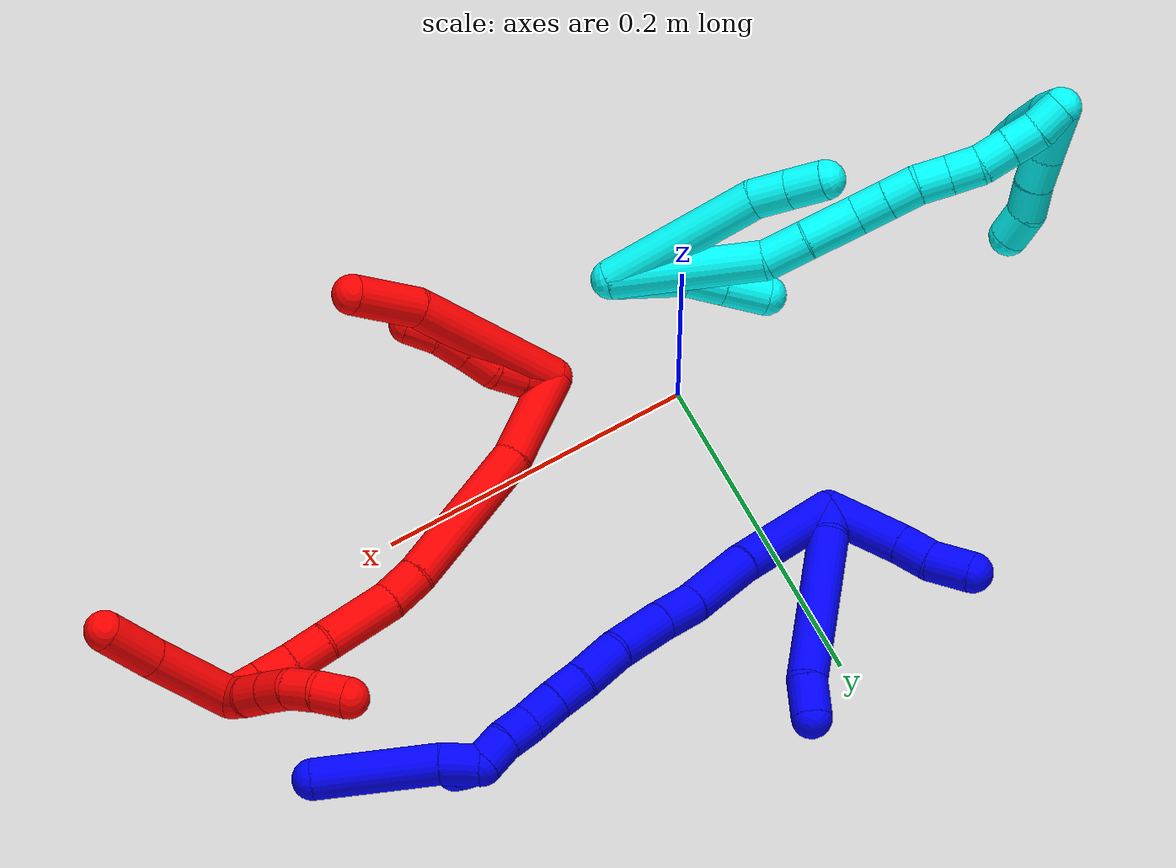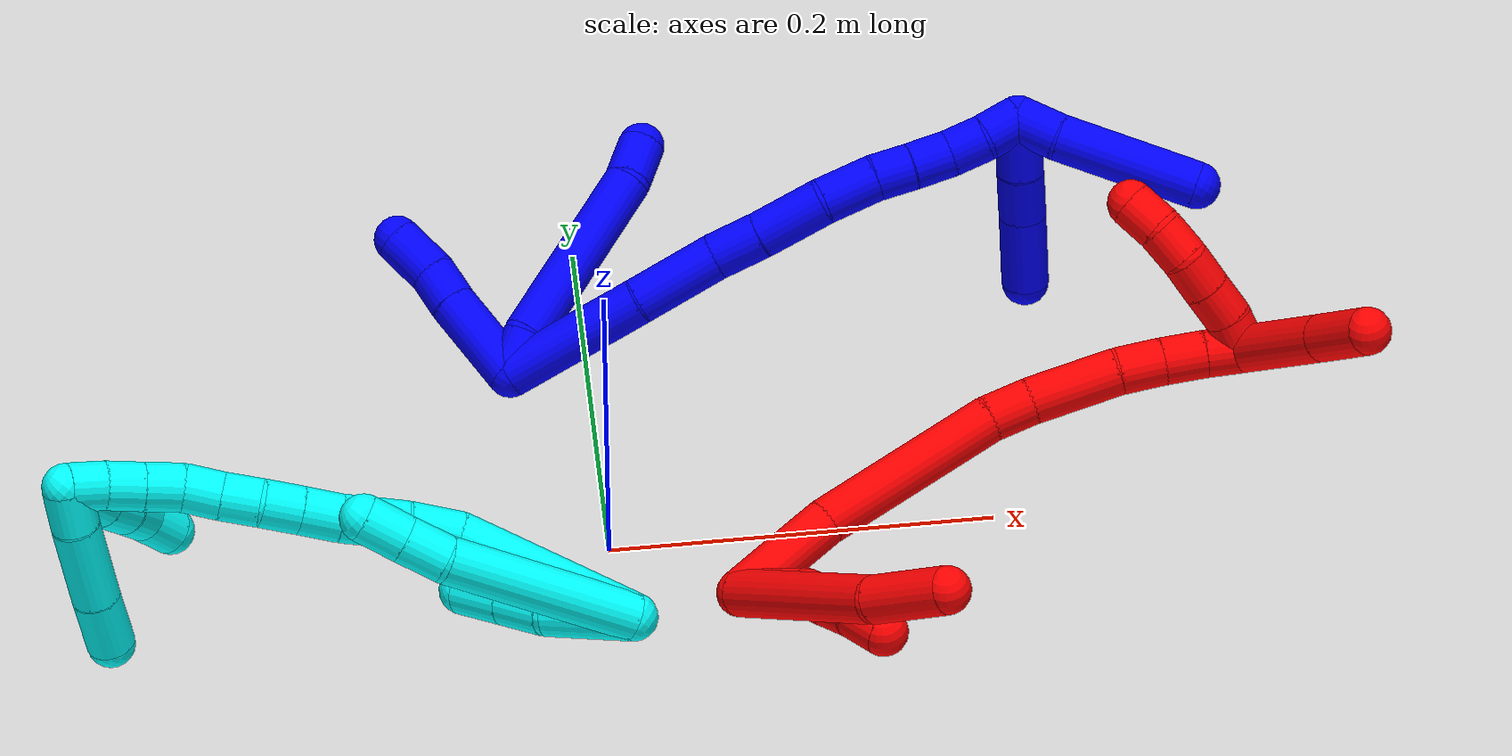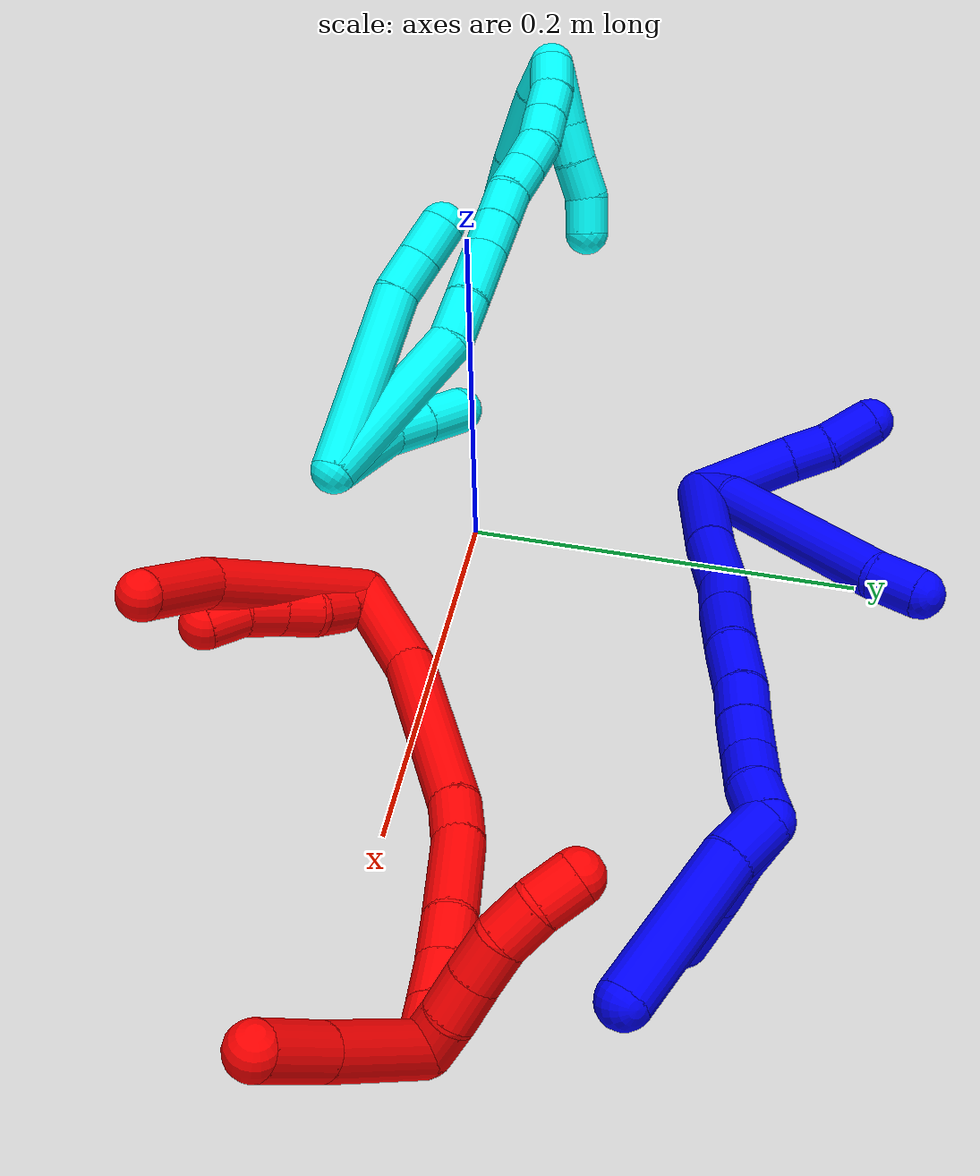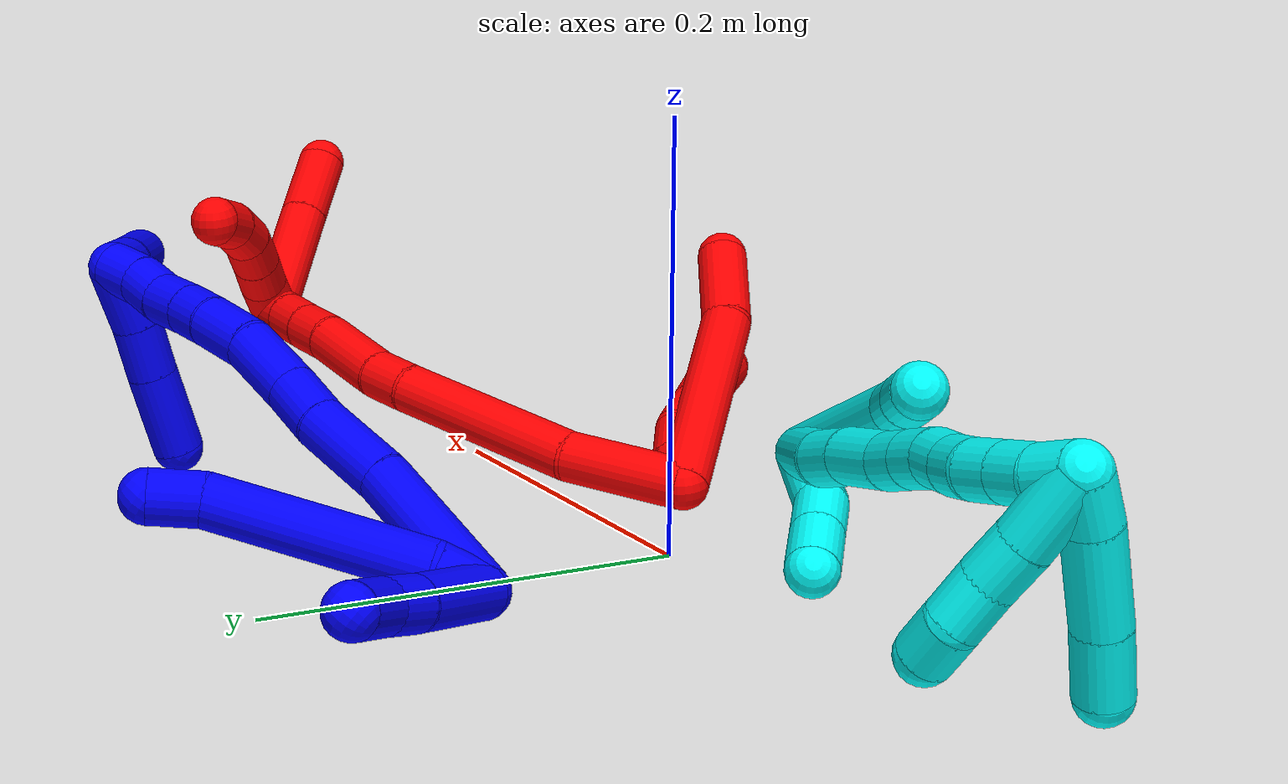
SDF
<sdf version="1.7">
 <world name="default">
  <plugin name="TubeGeneratorPlugin" filename="libtube_generator_plugin.so"/>
  <model name="photoneo_s_sensor">
   <static>1</static>
   <pose>0 0 2 1.57079 1.57079 3.14159</pose>
   <link name="link">
    <inertial><mass>0.1</mass></inertial>
    <sensor name="sensor" type="depth">
     <update_rate>30</update_rate>
     <camera>
      <horizontal_fov>1.22</horizontal_fov>
      <image><width>1920</width><height>1200</height><format>B8G8R8</format></image>
      <clip><near>0.1</near><far>4</far></clip>
      <depth_camera><output>points</output></depth_camera>
     </camera>
     <plugin name="camera_plugin" filename="libgazebo_ros_depth_camera.so">
      <baseline>0.2</baseline>
      <alwaysOn>1</alwaysOn>
      <updateRate>0.0</updateRate>
      <cameraName>camera_ir</cameraName>
      <imageTopicName>/camera/color/image_raw</imageTopicName>
      <cameraInfoTopicName>/camera/color/camera_info</cameraInfoTopicName>
      <depthImageTopicName>/camera/depth/image_raw</depthImageTopicName>
      <depthImageCameraInfoTopicName>/camera/depth/camera_info</depthImageCameraInfoTopicName>
      <pointCloudTopicName>/camera/depth/points</pointCloudTopicName>
      <frameName>fr_optical</frameName>
      <pointCloudCutoff>0.1</pointCloudCutoff>
      <pointCloudCutoffMax>2.0</pointCloudCutoffMax>
      <distortionK1>0</distortionK1>
      <distortionK2>0</distortionK2>
      <distortionK3>0</distortionK3>
      <distortionT1>0</distortionT1>
      <distortionT2>0</distortionT2>
      <CxPrime>0</CxPrime>
      <Cx>0</Cx>
      <Cy>0</Cy>
      <focalLength>0</focalLength>
      <hackBaseline>0</hackBaseline>
     </plugin>
    </sensor>
   </link>
  </model>
  <gravity>0 0 -9.8</gravity>
  <magnetic_field>6e-06 2.3e-05 -4.2e-05</magnetic_field>
  <atmosphere type="adiabatic"/>
  <physics name="default_physics" default="0" type="ode">
   <max_step_size>0.003</max_step_size>
   <real_time_factor>1</real_time_factor>
   <real_time_update_rate>1000</real_time_update_rate>
   <max_contacts>10000</max_contacts>
   <ode>
    <solver>
     <type>quick</type>
     <iters>100</iters>
     <sor>1.3</sor>
     <use_dynamic_moi_rescaling>0</use_dynamic_moi_rescaling>
    </solver>
    <constraints>
     <contact_max_correcting_vel>0</contact_max_correcting_vel>
     <contact_surface_layer>0.001</contact_surface_layer>
     <cfm>0</cfm>
     <erp>0.2</erp>
    </constraints>
   </ode>
  </physics>
  <scene><ambient>0.4 0.4 0.4 1</ambient><background>0.7 0.7 0.7 1</background><shadows>0</shadows></scene>
  <audio><device>default</device></audio>
  <spherical_coordinates>
   <surface_model>EARTH_WGS84</surface_model>
   <latitude_deg>0</latitude_deg>
   <longitude_deg>0</longitude_deg>
   <elevation>0</elevation>
   <heading_deg>0</heading_deg>
  </spherical_coordinates>
  <model name="bin">
   <static>1</static>
   <link name="bottom">
    <collision name="collision-bottom">
     <pose>0 0 -0.01 0 -0 0</pose>
     <geometry><box><size>0.8 0.6 0.02</size></box></geometry>
     <surface>
      <friction><ode><mu>100</mu><mu2>100</mu2></ode></friction>
      <contact><collide_bitmask>65535</collide_bitmask></contact>
     </surface>
    </collision>
   </link>
   <link name="west_wall">
    <collision name="collision-west_wall">
     <pose>-0.41 0 0.1 0 -0 0</pose>
     <geometry><box><size>0.02 0.6 0.2</size></box></geometry>
     <surface>
      <friction><ode><mu>100</mu><mu2>100</mu2></ode></friction>
      <contact><collide_bitmask>65535</collide_bitmask></contact>
     </surface>
    </collision>
   </link>
   <link name="east_wall">
    <collision name="collision-east_wall">
     <pose>0.41 0 0.1 0 -0 0</pose>
     <geometry><box><size>0.02 0.6 0.2</size></box></geometry>
     <surface>
      <friction><ode><mu>100</mu><mu2>100</mu2></ode></friction>
      <contact><collide_bitmask>65535</collide_bitmask></contact>
     </surface>
    </collision>
   </link>
   <link name="south_wall">
    <collision name="collision-south_wall">
     <pose>0 -0.31 0.1 0 -0 0</pose>
     <geometry><box><size>0.8 0.02 0.2</size></box></geometry>
     <surface>
      <friction><ode><mu>100</mu><mu2>100</mu2></ode></friction>
      <contact><collide_bitmask>65535</collide_bitmask></contact>
     </surface>
    </collision>
   </link>
   <link name="north_wall">
    <collision name="collision-north_wall">
     <pose>0 0.31 0.1 0 -0 0</pose>
     <geometry><box><size>0.8 0.02 0.2</size></box></geometry>
     <surface>
      <friction><ode><mu>100</mu><mu2>100</mu2></ode></friction>
      <contact><collide_bitmask>65535</collide_bitmask></contact>
     </surface>
    </collision>
   </link>
  </model>
  <model name="1">
   <static>0</static>
   <link name="1">
    <collision name="collision-cylinder-e_1_2_8">
     <pose>-0.002616 0.00253 0.010844 -0.229179 -0.230747 0.026674</pose>
     <geometry><cylinder><radius>0.0125</radius><length>0.022877</length></cylinder></geometry>
     <surface>
      <friction><ode><mu>1.16</mu><mu2>1.16</mu2><slip1>0</slip1><slip2>0</slip2></ode></friction>
      <contact><ode><kp>1e+06</kp><kd>1</kd><max_vel>0</max_vel><min_depth>0.001</min_depth></ode></contact>
     </surface>
    </collision>
    <visual name="visual-cylinder-e_1_2_8">
     <pose>-0.002616 0.00253 0.010844 -0.229179 -0.230747 0.026674</pose>
     <geometry><cylinder><radius>0.0125</radius><length>0.022877</length></cylinder></geometry>
     <material><ambient>0 0 1 1</ambient></material>
    </visual>
    <collision name="collision-cylinder-e_2_8_9">
     <pose>-0.008558 0.025469 0.068619 -0.410225 -0.064892 0.013505</pose>
     <geometry><cylinder><radius>0.0125</radius><length>0.102569</length></cylinder></geometry>
     <surface>
      <friction><ode><mu>1.16</mu><mu2>1.16</mu2><slip1>0</slip1><slip2>0</slip2></ode></friction>
      <contact><ode><kp>1e+06</kp><kd>1</kd><max_vel>0</max_vel><min_depth>0.001</min_depth></ode></contact>
     </surface>
    </collision>
    <visual name="visual-cylinder-e_2_8_9">
     <pose>-0.008558 0.025469 0.068619 -0.410225 -0.064892 0.013505</pose>
     <geometry><cylinder><radius>0.0125</radius><length>0.102569</length></cylinder></geometry>
     <material><ambient>0 0 1 1</ambient></material>
    </visual>
    <collision name="collision-cylinder-e_3_9_6">
     <pose>-0.015114 0.052819 0.125147 -0.626029 -0.266292 0.086645</pose>
     <geometry><cylinder><radius>0.0125</radius><length>0.024554</length></cylinder></geometry>
     <surface>
      <friction><ode><mu>1.16</mu><mu2>1.16</mu2><slip1>0</slip1><slip2>0</slip2></ode></friction>
      <contact><ode><kp>1e+06</kp><kd>1</kd><max_vel>0</max_vel><min_depth>0.001</min_depth></ode></contact>
     </surface>
    </collision>
    <visual name="visual-cylinder-e_3_9_6">
     <pose>-0.015114 0.052819 0.125147 -0.626029 -0.266292 0.086645</pose>
     <geometry><cylinder><radius>0.0125</radius><length>0.024554</length></cylinder></geometry>
     <material><ambient>0 0 1 1</ambient></material>
    </visual>
    <collision name="collision-cylinder-e_1_2_10">
     <pose>-0.023883 0.006995 0.006105 -0.85325 -1.20003 0.602997</pose>
     <geometry><cylinder><radius>0.0125</radius><length>0.051249</length></cylinder></geometry>
     <surface>
      <friction><ode><mu>1.16</mu><mu2>1.16</mu2><slip1>0</slip1><slip2>0</slip2></ode></friction>
      <contact><ode><kp>1e+06</kp><kd>1</kd><max_vel>0</max_vel><min_depth>0.001</min_depth></ode></contact>
     </surface>
    </collision>
    <visual name="visual-cylinder-e_1_2_10">
     <pose>-0.023883 0.006995 0.006105 -0.85325 -1.20003 0.602997</pose>
     <geometry><cylinder><radius>0.0125</radius><length>0.051249</length></cylinder></geometry>
     <material><ambient>0 0 1 1</ambient></material>
    </visual>
    <collision name="collision-cylinder-e_2_10_11">
     <pose>-0.057421 0.017062 0.015618 -0.733587 -1.12718 0.476354</pose>
     <geometry><cylinder><radius>0.0125</radius><length>0.021379</length></cylinder></geometry>
     <surface>
      <friction><ode><mu>1.16</mu><mu2>1.16</mu2><slip1>0</slip1><slip2>0</slip2></ode></friction>
      <contact><ode><kp>1e+06</kp><kd>1</kd><max_vel>0</max_vel><min_depth>0.001</min_depth></ode></contact>
     </surface>
    </collision>
    <visual name="visual-cylinder-e_2_10_11">
     <pose>-0.057421 0.017062 0.015618 -0.733587 -1.12718 0.476354</pose>
     <geometry><cylinder><radius>0.0125</radius><length>0.021379</length></cylinder></geometry>
     <material><ambient>0 0 1 1</ambient></material>
    </visual>
    <collision name="collision-cylinder-e_3_11_5">
     <pose>-0.080452 0.022167 0.021093 -0.777122 -1.35732 0.637742</pose>
     <geometry><cylinder><radius>0.0125</radius><length>0.027372</length></cylinder></geometry>
     <surface>
      <friction><ode><mu>1.16</mu><mu2>1.16</mu2><slip1>0</slip1><slip2>0</slip2></ode></friction>
      <contact><ode><kp>1e+06</kp><kd>1</kd><max_vel>0</max_vel><min_depth>0.001</min_depth></ode></contact>
     </surface>
    </collision>
    <visual name="visual-cylinder-e_3_11_5">
     <pose>-0.080452 0.022167 0.021093 -0.777122 -1.35732 0.637742</pose>
     <geometry><cylinder><radius>0.0125</radius><length>0.027372</length></cylinder></geometry>
     <material><ambient>0 0 1 1</ambient></material>
    </visual>
    <collision name="collision-cylinder-e_1_2_12">
     <pose>0.017679 -0.001946 0.034822 0.055823 0.469166 0.013344</pose>
     <geometry><cylinder><radius>0.0125</radius><length>0.078203</length></cylinder></geometry>
     <surface>
      <friction><ode><mu>1.16</mu><mu2>1.16</mu2><slip1>0</slip1><slip2>0</slip2></ode></friction>
      <contact><ode><kp>1e+06</kp><kd>1</kd><max_vel>0</max_vel><min_depth>0.001</min_depth></ode></contact>
     </surface>
    </collision>
    <visual name="visual-cylinder-e_1_2_12">
     <pose>0.017679 -0.001946 0.034822 0.055823 0.469166 0.013344</pose>
     <geometry><cylinder><radius>0.0125</radius><length>0.078203</length></cylinder></geometry>
     <material><ambient>0 0 1 1</ambient></material>
    </visual>
    <collision name="collision-cylinder-e_2_12_13">
     <pose>0.045502 -0.002468 0.090483 -0.068232 0.452071 -0.015697</pose>
     <geometry><cylinder><radius>0.0125</radius><length>0.046441</length></cylinder></geometry>
     <surface>
      <friction><ode><mu>1.16</mu><mu2>1.16</mu2><slip1>0</slip1><slip2>0</slip2></ode></friction>
      <contact><ode><kp>1e+06</kp><kd>1</kd><max_vel>0</max_vel><min_depth>0.001</min_depth></ode></contact>
     </surface>
    </collision>
    <visual name="visual-cylinder-e_2_12_13">
     <pose>0.045502 -0.002468 0.090483 -0.068232 0.452071 -0.015697</pose>
     <geometry><cylinder><radius>0.0125</radius><length>0.046441</length></cylinder></geometry>
     <material><ambient>0 0 1 1</ambient></material>
    </visual>
    <collision name="collision-cylinder-e_3_13_14">
     <pose>0.062421 -0.001557 0.122607 0.045458 0.540268 0.012589</pose>
     <geometry><cylinder><radius>0.0125</radius><length>0.026345</length></cylinder></geometry>
     <surface>
      <friction><ode><mu>1.16</mu><mu2>1.16</mu2><slip1>0</slip1><slip2>0</slip2></ode></friction>
      <contact><ode><kp>1e+06</kp><kd>1</kd><max_vel>0</max_vel><min_depth>0.001</min_depth></ode></contact>
     </surface>
    </collision>
    <visual name="visual-cylinder-e_3_13_14">
     <pose>0.062421 -0.001557 0.122607 0.045458 0.540268 0.012589</pose>
     <geometry><cylinder><radius>0.0125</radius><length>0.026345</length></cylinder></geometry>
     <material><ambient>0 0 1 1</ambient></material>
    </visual>
    <collision name="collision-cylinder-e_4_14_15">
     <pose>0.077891 -0.002298 0.150288 0.013897 0.487504 0.003456</pose>
     <geometry><cylinder><radius>0.0125</radius><length>0.037121</length></cylinder></geometry>
     <surface>
      <friction><ode><mu>1.16</mu><mu2>1.16</mu2><slip1>0</slip1><slip2>0</slip2></ode></friction>
      <contact><ode><kp>1e+06</kp><kd>1</kd><max_vel>0</max_vel><min_depth>0.001</min_depth></ode></contact>
     </surface>
    </collision>
    <visual name="visual-cylinder-e_4_14_15">
     <pose>0.077891 -0.002298 0.150288 0.013897 0.487504 0.003456</pose>
     <geometry><cylinder><radius>0.0125</radius><length>0.037121</length></cylinder></geometry>
     <material><ambient>0 0 1 1</ambient></material>
    </visual>
    <collision name="collision-cylinder-e_5_15_16">
     <pose>0.094089 0.00034 0.179168 -0.225711 0.529997 -0.061496</pose>
     <geometry><cylinder><radius>0.0125</radius><length>0.029687</length></cylinder></geometry>
     <surface>
      <friction><ode><mu>1.16</mu><mu2>1.16</mu2><slip1>0</slip1><slip2>0</slip2></ode></friction>
      <contact><ode><kp>1e+06</kp><kd>1</kd><max_vel>0</max_vel><min_depth>0.001</min_depth></ode></contact>
     </surface>
    </collision>
    <visual name="visual-cylinder-e_5_15_16">
     <pose>0.094089 0.00034 0.179168 -0.225711 0.529997 -0.061496</pose>
     <geometry><cylinder><radius>0.0125</radius><length>0.029687</length></cylinder></geometry>
     <material><ambient>0 0 1 1</ambient></material>
    </visual>
    <collision name="collision-cylinder-e_6_16_17">
     <pose>0.107632 0.005416 0.199364 -0.278916 0.645246 -0.093783</pose>
     <geometry><cylinder><radius>0.0125</radius><length>0.020086</length></cylinder></geometry>
     <surface>
      <friction><ode><mu>1.16</mu><mu2>1.16</mu2><slip1>0</slip1><slip2>0</slip2></ode></friction>
      <contact><ode><kp>1e+06</kp><kd>1</kd><max_vel>0</max_vel><min_depth>0.001</min_depth></ode></contact>
     </surface>
    </collision>
    <visual name="visual-cylinder-e_6_16_17">
     <pose>0.107632 0.005416 0.199364 -0.278916 0.645246 -0.093783</pose>
     <geometry><cylinder><radius>0.0125</radius><length>0.020086</length></cylinder></geometry>
     <material><ambient>0 0 1 1</ambient></material>
    </visual>
    <collision name="collision-cylinder-e_7_17_18">
     <pose>0.1198 0.010506 0.215469 -0.33074 0.604412 -0.103966</pose>
     <geometry><cylinder><radius>0.0125</radius><length>0.021566</length></cylinder></geometry>
     <surface>
      <friction><ode><mu>1.16</mu><mu2>1.16</mu2><slip1>0</slip1><slip2>0</slip2></ode></friction>
      <contact><ode><kp>1e+06</kp><kd>1</kd><max_vel>0</max_vel><min_depth>0.001</min_depth></ode></contact>
     </surface>
    </collision>
    <visual name="visual-cylinder-e_7_17_18">
     <pose>0.1198 0.010506 0.215469 -0.33074 0.604412 -0.103966</pose>
     <geometry><cylinder><radius>0.0125</radius><length>0.021566</length></cylinder></geometry>
     <material><ambient>0 0 1 1</ambient></material>
    </visual>
    <collision name="collision-cylinder-e_8_18_19">
     <pose>0.131211 0.014397 0.23244 -0.117124 0.548873 -0.03301</pose>
     <geometry><cylinder><radius>0.0125</radius><length>0.020252</length></cylinder></geometry>
     <surface>
      <friction><ode><mu>1.16</mu><mu2>1.16</mu2><slip1>0</slip1><slip2>0</slip2></ode></friction>
      <contact><ode><kp>1e+06</kp><kd>1</kd><max_vel>0</max_vel><min_depth>0.001</min_depth></ode></contact>
     </surface>
    </collision>
    <visual name="visual-cylinder-e_8_18_19">
     <pose>0.131211 0.014397 0.23244 -0.117124 0.548873 -0.03301</pose>
     <geometry><cylinder><radius>0.0125</radius><length>0.020252</length></cylinder></geometry>
     <material><ambient>0 0 1 1</ambient></material>
    </visual>
    <collision name="collision-cylinder-e_9_19_1">
     <pose>0.140683 0.018088 0.249867 -0.294275 0.425493 -0.064009</pose>
     <geometry><cylinder><radius>0.0125</radius><length>0.020299</length></cylinder></geometry>
     <surface>
      <friction><ode><mu>1.16</mu><mu2>1.16</mu2><slip1>0</slip1><slip2>0</slip2></ode></friction>
      <contact><ode><kp>1e+06</kp><kd>1</kd><max_vel>0</max_vel><min_depth>0.001</min_depth></ode></contact>
     </surface>
    </collision>
    <visual name="visual-cylinder-e_9_19_1">
     <pose>0.140683 0.018088 0.249867 -0.294275 0.425493 -0.064009</pose>
     <geometry><cylinder><radius>0.0125</radius><length>0.020299</length></cylinder></geometry>
     <material><ambient>0 0 1 1</ambient></material>
    </visual>
    <collision name="collision-cylinder-e_1_1_20">
     <pose>0.152284 0.028909 0.247542 -2.51195 0.492152 -1.31395</pose>
     <geometry><cylinder><radius>0.0125</radius><length>0.031368</length></cylinder></geometry>
     <surface>
      <friction><ode><mu>1.16</mu><mu2>1.16</mu2><slip1>0</slip1><slip2>0</slip2></ode></friction>
      <contact><ode><kp>1e+06</kp><kd>1</kd><max_vel>0</max_vel><min_depth>0.001</min_depth></ode></contact>
     </surface>
    </collision>
    <visual name="visual-cylinder-e_1_1_20">
     <pose>0.152284 0.028909 0.247542 -2.51195 0.492152 -1.31395</pose>
     <geometry><cylinder><radius>0.0125</radius><length>0.031368</length></cylinder></geometry>
     <material><ambient>0 0 1 1</ambient></material>
    </visual>
    <collision name="collision-cylinder-e_2_20_21">
     <pose>0.165665 0.044832 0.227298 -2.43243 0.463182 -1.13432</pose>
     <geometry><cylinder><radius>0.0125</radius><length>0.026722</length></cylinder></geometry>
     <surface>
      <friction><ode><mu>1.16</mu><mu2>1.16</mu2><slip1>0</slip1><slip2>0</slip2></ode></friction>
      <contact><ode><kp>1e+06</kp><kd>1</kd><max_vel>0</max_vel><min_depth>0.001</min_depth></ode></contact>
     </surface>
    </collision>
    <visual name="visual-cylinder-e_2_20_21">
     <pose>0.165665 0.044832 0.227298 -2.43243 0.463182 -1.13432</pose>
     <geometry><cylinder><radius>0.0125</radius><length>0.026722</length></cylinder></geometry>
     <material><ambient>0 0 1 1</ambient></material>
    </visual>
    <collision name="collision-cylinder-e_3_21_4">
     <pose>0.181065 0.06431 0.203618 -2.4666 0.466805 -1.19087</pose>
     <geometry><cylinder><radius>0.0125</radius><length>0.041909</length></cylinder></geometry>
     <surface>
      <friction><ode><mu>1.16</mu><mu2>1.16</mu2><slip1>0</slip1><slip2>0</slip2></ode></friction>
      <contact><ode><kp>1e+06</kp><kd>1</kd><max_vel>0</max_vel><min_depth>0.001</min_depth></ode></contact>
     </surface>
    </collision>
    <visual name="visual-cylinder-e_3_21_4">
     <pose>0.181065 0.06431 0.203618 -2.4666 0.466805 -1.19087</pose>
     <geometry><cylinder><radius>0.0125</radius><length>0.041909</length></cylinder></geometry>
     <material><ambient>0 0 1 1</ambient></material>
    </visual>
    <collision name="collision-cylinder-e_1_1_22">
     <pose>0.156651 0.01974 0.260729 0.472107 1.38104 0.392357</pose>
     <geometry><cylinder><radius>0.0125</radius><length>0.023988</length></cylinder></geometry>
     <surface>
      <friction><ode><mu>1.16</mu><mu2>1.16</mu2><slip1>0</slip1><slip2>0</slip2></ode></friction>
      <contact><ode><kp>1e+06</kp><kd>1</kd><max_vel>0</max_vel><min_depth>0.001</min_depth></ode></contact>
     </surface>
    </collision>
    <visual name="visual-cylinder-e_1_1_22">
     <pose>0.156651 0.01974 0.260729 0.472107 1.38104 0.392357</pose>
     <geometry><cylinder><radius>0.0125</radius><length>0.023988</length></cylinder></geometry>
     <material><ambient>0 0 1 1</ambient></material>
    </visual>
    <collision name="collision-cylinder-e_2_22_3">
     <pose>0.205151 0.020291 0.272415 -0.161855 1.31002 -0.124438</pose>
     <geometry><cylinder><radius>0.0125</radius><length>0.076012</length></cylinder></geometry>
     <surface>
      <friction><ode><mu>1.16</mu><mu2>1.16</mu2><slip1>0</slip1><slip2>0</slip2></ode></friction>
      <contact><ode><kp>1e+06</kp><kd>1</kd><max_vel>0</max_vel><min_depth>0.001</min_depth></ode></contact>
     </surface>
    </collision>
    <visual name="visual-cylinder-e_2_22_3">
     <pose>0.205151 0.020291 0.272415 -0.161855 1.31002 -0.124438</pose>
     <geometry><cylinder><radius>0.0125</radius><length>0.076012</length></cylinder></geometry>
     <material><ambient>0 0 1 1</ambient></material>
    </visual>
    <collision name="collision-sphere-3">
     <pose>0.241872 0.02187 0.282086 0 -0 0</pose>
     <geometry><sphere><radius>0.0125</radius></sphere></geometry>
     <surface>
      <friction><ode><mu>1.16</mu><mu2>1.16</mu2><slip1>0</slip1><slip2>0</slip2></ode></friction>
      <contact><ode><kp>1e+06</kp><kd>1</kd><max_vel>0</max_vel><min_depth>0.001</min_depth></ode></contact>
     </surface>
    </collision>
    <visual name="visual-sphere-3">
     <pose>0.241872 0.02187 0.282086 0 -0 0</pose>
     <geometry><sphere><radius>0.0125</radius></sphere></geometry>
     <material><ambient>0 0 1 1</ambient></material>
    </visual>
    <collision name="collision-sphere-22">
     <pose>0.16843 0.018711 0.262744 0 -0 0</pose>
     <geometry><sphere><radius>0.0125</radius></sphere></geometry>
     <surface>
      <friction><ode><mu>1.16</mu><mu2>1.16</mu2><slip1>0</slip1><slip2>0</slip2></ode></friction>
      <contact><ode><kp>1e+06</kp><kd>1</kd><max_vel>0</max_vel><min_depth>0.001</min_depth></ode></contact>
     </surface>
    </collision>
    <visual name="visual-sphere-22">
     <pose>0.16843 0.018711 0.262744 0 -0 0</pose>
     <geometry><sphere><radius>0.0125</radius></sphere></geometry>
     <material><ambient>0 0 1 1</ambient></material>
    </visual>
    <collision name="collision-sphere-4">
     <pose>0.190495 0.076003 0.189009 0 -0 0</pose>
     <geometry><sphere><radius>0.0125</radius></sphere></geometry>
     <surface>
      <friction><ode><mu>1.16</mu><mu2>1.16</mu2><slip1>0</slip1><slip2>0</slip2></ode></friction>
      <contact><ode><kp>1e+06</kp><kd>1</kd><max_vel>0</max_vel><min_depth>0.001</min_depth></ode></contact>
     </surface>
    </collision>
    <visual name="visual-sphere-4">
     <pose>0.190495 0.076003 0.189009 0 -0 0</pose>
     <geometry><sphere><radius>0.0125</radius></sphere></geometry>
     <material><ambient>0 0 1 1</ambient></material>
    </visual>
    <collision name="collision-sphere-21">
     <pose>0.171634 0.052616 0.218227 0 -0 0</pose>
     <geometry><sphere><radius>0.0125</radius></sphere></geometry>
     <surface>
      <friction><ode><mu>1.16</mu><mu2>1.16</mu2><slip1>0</slip1><slip2>0</slip2></ode></friction>
      <contact><ode><kp>1e+06</kp><kd>1</kd><max_vel>0</max_vel><min_depth>0.001</min_depth></ode></contact>
     </surface>
    </collision>
    <visual name="visual-sphere-21">
     <pose>0.171634 0.052616 0.218227 0 -0 0</pose>
     <geometry><sphere><radius>0.0125</radius></sphere></geometry>
     <material><ambient>0 0 1 1</ambient></material>
    </visual>
    <collision name="collision-sphere-20">
     <pose>0.159695 0.037048 0.23637 0 -0 0</pose>
     <geometry><sphere><radius>0.0125</radius></sphere></geometry>
     <surface>
      <friction><ode><mu>1.16</mu><mu2>1.16</mu2><slip1>0</slip1><slip2>0</slip2></ode></friction>
      <contact><ode><kp>1e+06</kp><kd>1</kd><max_vel>0</max_vel><min_depth>0.001</min_depth></ode></contact>
     </surface>
    </collision>
    <visual name="visual-sphere-20">
     <pose>0.159695 0.037048 0.23637 0 -0 0</pose>
     <geometry><sphere><radius>0.0125</radius></sphere></geometry>
     <material><ambient>0 0 1 1</ambient></material>
    </visual>
    <collision name="collision-sphere-11">
     <pose>-0.067076 0.020134 0.019026 0 -0 0</pose>
     <geometry><sphere><radius>0.0125</radius></sphere></geometry>
     <surface>
      <friction><ode><mu>1.16</mu><mu2>1.16</mu2><slip1>0</slip1><slip2>0</slip2></ode></friction>
      <contact><ode><kp>1e+06</kp><kd>1</kd><max_vel>0</max_vel><min_depth>0.001</min_depth></ode></contact>
     </surface>
    </collision>
    <visual name="visual-sphere-11">
     <pose>-0.067076 0.020134 0.019026 0 -0 0</pose>
     <geometry><sphere><radius>0.0125</radius></sphere></geometry>
     <material><ambient>0 0 1 1</ambient></material>
    </visual>
    <collision name="collision-sphere-10">
     <pose>-0.047766 0.01399 0.01221 0 -0 0</pose>
     <geometry><sphere><radius>0.0125</radius></sphere></geometry>
     <surface>
      <friction><ode><mu>1.16</mu><mu2>1.16</mu2><slip1>0</slip1><slip2>0</slip2></ode></friction>
      <contact><ode><kp>1e+06</kp><kd>1</kd><max_vel>0</max_vel><min_depth>0.001</min_depth></ode></contact>
     </surface>
    </collision>
    <visual name="visual-sphere-10">
     <pose>-0.047766 0.01399 0.01221 0 -0 0</pose>
     <geometry><sphere><radius>0.0125</radius></sphere></geometry>
     <material><ambient>0 0 1 1</ambient></material>
    </visual>
    <collision name="collision-sphere-6">
     <pose>-0.018345 0.059759 0.134746 0 -0 0</pose>
     <geometry><sphere><radius>0.0125</radius></sphere></geometry>
     <surface>
      <friction><ode><mu>1.16</mu><mu2>1.16</mu2><slip1>0</slip1><slip2>0</slip2></ode></friction>
      <contact><ode><kp>1e+06</kp><kd>1</kd><max_vel>0</max_vel><min_depth>0.001</min_depth></ode></contact>
     </surface>
    </collision>
    <visual name="visual-sphere-6">
     <pose>-0.018345 0.059759 0.134746 0 -0 0</pose>
     <geometry><sphere><radius>0.0125</radius></sphere></geometry>
     <material><ambient>0 0 1 1</ambient></material>
    </visual>
    <collision name="collision-sphere-9">
     <pose>-0.011883 0.045879 0.115549 0 -0 0</pose>
     <geometry><sphere><radius>0.0125</radius></sphere></geometry>
     <surface>
      <friction><ode><mu>1.16</mu><mu2>1.16</mu2><slip1>0</slip1><slip2>0</slip2></ode></friction>
      <contact><ode><kp>1e+06</kp><kd>1</kd><max_vel>0</max_vel><min_depth>0.001</min_depth></ode></contact>
     </surface>
    </collision>
    <visual name="visual-sphere-9">
     <pose>-0.011883 0.045879 0.115549 0 -0 0</pose>
     <geometry><sphere><radius>0.0125</radius></sphere></geometry>
     <material><ambient>0 0 1 1</ambient></material>
    </visual>
    <collision name="collision-sphere-2">
     <geometry><sphere><radius>0.0125</radius></sphere></geometry>
     <surface>
      <friction><ode><mu>1.16</mu><mu2>1.16</mu2><slip1>0</slip1><slip2>0</slip2></ode></friction>
      <contact><ode><kp>1e+06</kp><kd>1</kd><max_vel>0</max_vel><min_depth>0.001</min_depth></ode></contact>
     </surface>
    </collision>
    <visual name="visual-sphere-2">
     <geometry><sphere><radius>0.0125</radius></sphere></geometry>
     <material><ambient>0 0 1 1</ambient></material>
    </visual>
    <collision name="collision-sphere-19">
     <pose>0.136494 0.015406 0.24102 0 -0 0</pose>
     <geometry><sphere><radius>0.0125</radius></sphere></geometry>
     <surface>
      <friction><ode><mu>1.16</mu><mu2>1.16</mu2><slip1>0</slip1><slip2>0</slip2></ode></friction>
      <contact><ode><kp>1e+06</kp><kd>1</kd><max_vel>0</max_vel><min_depth>0.001</min_depth></ode></contact>
     </surface>
    </collision>
    <visual name="visual-sphere-19">
     <pose>0.136494 0.015406 0.24102 0 -0 0</pose>
     <geometry><sphere><radius>0.0125</radius></sphere></geometry>
     <material><ambient>0 0 1 1</ambient></material>
    </visual>
    <collision name="collision-sphere-8">
     <pose>-0.005232 0.005059 0.021688 0 -0 0</pose>
     <geometry><sphere><radius>0.0125</radius></sphere></geometry>
     <surface>
      <friction><ode><mu>1.16</mu><mu2>1.16</mu2><slip1>0</slip1><slip2>0</slip2></ode></friction>
      <contact><ode><kp>1e+06</kp><kd>1</kd><max_vel>0</max_vel><min_depth>0.001</min_depth></ode></contact>
     </surface>
    </collision>
    <visual name="visual-sphere-8">
     <pose>-0.005232 0.005059 0.021688 0 -0 0</pose>
     <geometry><sphere><radius>0.0125</radius></sphere></geometry>
     <material><ambient>0 0 1 1</ambient></material>
    </visual>
    <collision name="collision-sphere-5">
     <pose>-0.093827 0.024201 0.02316 0 -0 0</pose>
     <geometry><sphere><radius>0.0125</radius></sphere></geometry>
     <surface>
      <friction><ode><mu>1.16</mu><mu2>1.16</mu2><slip1>0</slip1><slip2>0</slip2></ode></friction>
      <contact><ode><kp>1e+06</kp><kd>1</kd><max_vel>0</max_vel><min_depth>0.001</min_depth></ode></contact>
     </surface>
    </collision>
    <visual name="visual-sphere-5">
     <pose>-0.093827 0.024201 0.02316 0 -0 0</pose>
     <geometry><sphere><radius>0.0125</radius></sphere></geometry>
     <material><ambient>0 0 1 1</ambient></material>
    </visual>
    <collision name="collision-sphere-12">
     <pose>0.035359 -0.003892 0.069644 0 -0 0</pose>
     <geometry><sphere><radius>0.0125</radius></sphere></geometry>
     <surface>
      <friction><ode><mu>1.16</mu><mu2>1.16</mu2><slip1>0</slip1><slip2>0</slip2></ode></friction>
      <contact><ode><kp>1e+06</kp><kd>1</kd><max_vel>0</max_vel><min_depth>0.001</min_depth></ode></contact>
     </surface>
    </collision>
    <visual name="visual-sphere-12">
     <pose>0.035359 -0.003892 0.069644 0 -0 0</pose>
     <geometry><sphere><radius>0.0125</radius></sphere></geometry>
     <material><ambient>0 0 1 1</ambient></material>
    </visual>
    <collision name="collision-sphere-13">
     <pose>0.055646 -0.001044 0.111322 0 -0 0</pose>
     <geometry><sphere><radius>0.0125</radius></sphere></geometry>
     <surface>
      <friction><ode><mu>1.16</mu><mu2>1.16</mu2><slip1>0</slip1><slip2>0</slip2></ode></friction>
      <contact><ode><kp>1e+06</kp><kd>1</kd><max_vel>0</max_vel><min_depth>0.001</min_depth></ode></contact>
     </surface>
    </collision>
    <visual name="visual-sphere-13">
     <pose>0.055646 -0.001044 0.111322 0 -0 0</pose>
     <geometry><sphere><radius>0.0125</radius></sphere></geometry>
     <material><ambient>0 0 1 1</ambient></material>
    </visual>
    <collision name="collision-sphere-14">
     <pose>0.069196 -0.00207 0.133892 0 -0 0</pose>
     <geometry><sphere><radius>0.0125</radius></sphere></geometry>
     <surface>
      <friction><ode><mu>1.16</mu><mu2>1.16</mu2><slip1>0</slip1><slip2>0</slip2></ode></friction>
      <contact><ode><kp>1e+06</kp><kd>1</kd><max_vel>0</max_vel><min_depth>0.001</min_depth></ode></contact>
     </surface>
    </collision>
    <visual name="visual-sphere-14">
     <pose>0.069196 -0.00207 0.133892 0 -0 0</pose>
     <geometry><sphere><radius>0.0125</radius></sphere></geometry>
     <material><ambient>0 0 1 1</ambient></material>
    </visual>
    <collision name="collision-sphere-15">
     <pose>0.086585 -0.002526 0.166685 0 -0 0</pose>
     <geometry><sphere><radius>0.0125</radius></sphere></geometry>
     <surface>
      <friction><ode><mu>1.16</mu><mu2>1.16</mu2><slip1>0</slip1><slip2>0</slip2></ode></friction>
      <contact><ode><kp>1e+06</kp><kd>1</kd><max_vel>0</max_vel><min_depth>0.001</min_depth></ode></contact>
     </surface>
    </collision>
    <visual name="visual-sphere-15">
     <pose>0.086585 -0.002526 0.166685 0 -0 0</pose>
     <geometry><sphere><radius>0.0125</radius></sphere></geometry>
     <material><ambient>0 0 1 1</ambient></material>
    </visual>
    <collision name="collision-sphere-16">
     <pose>0.101593 0.003207 0.19165 0 -0 0</pose>
     <geometry><sphere><radius>0.0125</radius></sphere></geometry>
     <surface>
      <friction><ode><mu>1.16</mu><mu2>1.16</mu2><slip1>0</slip1><slip2>0</slip2></ode></friction>
      <contact><ode><kp>1e+06</kp><kd>1</kd><max_vel>0</max_vel><min_depth>0.001</min_depth></ode></contact>
     </surface>
    </collision>
    <visual name="visual-sphere-16">
     <pose>0.101593 0.003207 0.19165 0 -0 0</pose>
     <geometry><sphere><radius>0.0125</radius></sphere></geometry>
     <material><ambient>0 0 1 1</ambient></material>
    </visual>
    <collision name="collision-sphere-17">
     <pose>0.113672 0.007625 0.207077 0 -0 0</pose>
     <geometry><sphere><radius>0.0125</radius></sphere></geometry>
     <surface>
      <friction><ode><mu>1.16</mu><mu2>1.16</mu2><slip1>0</slip1><slip2>0</slip2></ode></friction>
      <contact><ode><kp>1e+06</kp><kd>1</kd><max_vel>0</max_vel><min_depth>0.001</min_depth></ode></contact>
     </surface>
    </collision>
    <visual name="visual-sphere-17">
     <pose>0.113672 0.007625 0.207077 0 -0 0</pose>
     <geometry><sphere><radius>0.0125</radius></sphere></geometry>
     <material><ambient>0 0 1 1</ambient></material>
    </visual>
    <collision name="collision-sphere-18">
     <pose>0.125928 0.013387 0.223861 0 -0 0</pose>
     <geometry><sphere><radius>0.0125</radius></sphere></geometry>
     <surface>
      <friction><ode><mu>1.16</mu><mu2>1.16</mu2><slip1>0</slip1><slip2>0</slip2></ode></friction>
      <contact><ode><kp>1e+06</kp><kd>1</kd><max_vel>0</max_vel><min_depth>0.001</min_depth></ode></contact>
     </surface>
    </collision>
    <visual name="visual-sphere-18">
     <pose>0.125928 0.013387 0.223861 0 -0 0</pose>
     <geometry><sphere><radius>0.0125</radius></sphere></geometry>
     <material><ambient>0 0 1 1</ambient></material>
    </visual>
    <collision name="collision-sphere-1">
     <pose>0.144873 0.020769 0.258714 0 -0 0</pose>
     <geometry><sphere><radius>0.0125</radius></sphere></geometry>
     <surface>
      <friction><ode><mu>1.16</mu><mu2>1.16</mu2><slip1>0</slip1><slip2>0</slip2></ode></friction>
      <contact><ode><kp>1e+06</kp><kd>1</kd><max_vel>0</max_vel><min_depth>0.001</min_depth></ode></contact>
     </surface>
    </collision>
    <visual name="visual-sphere-1">
     <pose>0.144873 0.020769 0.258714 0 -0 0</pose>
     <geometry><sphere><radius>0.0125</radius></sphere></geometry>
     <material><ambient>0 0 1 1</ambient></material>
    </visual>
    <inertial>
     <pose>0.068353 0.016966 0.133868 0 -0 0</pose>
     <mass>0.75</mass>
     <inertia><ixx>0.000186</ixx><ixy>0</ixy><ixz>0</ixz><iyy>0.000223</iyy><iyz>0</iyz><izz>-8e-05</izz></inertia>
    </inertial>
   </link>
   <pose>-0.040563 0.113394 0.011805 -0.931277 0.267177 -0.660519</pose>
  </model>
  <model name="2">
   <static>0</static>
   <link name="2">
    <collision name="collision-cylinder-e_1_2_8">
     <pose>0.035819 -0.029021 0.023958 0.880672 0.760716 0.372425</pose>
     <geometry><cylinder><radius>0.0125</radius><length>0.103908</length></cylinder></geometry>
     <surface>
      <friction><ode><mu>1.16</mu><mu2>1.16</mu2><slip1>0</slip1><slip2>0</slip2></ode></friction>
      <contact><ode><kp>1e+06</kp><kd>1</kd><max_vel>0</max_vel><min_depth>0.001</min_depth></ode></contact>
     </surface>
    </collision>
    <visual name="visual-cylinder-e_1_2_8">
     <pose>0.035819 -0.029021 0.023958 0.880672 0.760716 0.372425</pose>
     <geometry><cylinder><radius>0.0125</radius><length>0.103908</length></cylinder></geometry>
     <material><ambient>1 0 0 1</ambient></material>
    </visual>
    <collision name="collision-cylinder-e_2_8_6">
     <pose>0.09078 -0.066143 0.05787 0.683137 0.980199 0.374879</pose>
     <geometry><cylinder><radius>0.0125</radius><length>0.046092</length></cylinder></geometry>
     <surface>
      <friction><ode><mu>1.16</mu><mu2>1.16</mu2><slip1>0</slip1><slip2>0</slip2></ode></friction>
      <contact><ode><kp>1e+06</kp><kd>1</kd><max_vel>0</max_vel><min_depth>0.001</min_depth></ode></contact>
     </surface>
    </collision>
    <visual name="visual-cylinder-e_2_8_6">
     <pose>0.09078 -0.066143 0.05787 0.683137 0.980199 0.374879</pose>
     <geometry><cylinder><radius>0.0125</radius><length>0.046092</length></cylinder></geometry>
     <material><ambient>1 0 0 1</ambient></material>
    </visual>
    <collision name="collision-cylinder-e_1_2_9">
     <pose>0.009327 -0.002811 0.002258 0.894058 1.20192 0.63506</pose>
     <geometry><cylinder><radius>0.0125</radius><length>0.02</length></cylinder></geometry>
     <surface>
      <friction><ode><mu>1.16</mu><mu2>1.16</mu2><slip1>0</slip1><slip2>0</slip2></ode></friction>
      <contact><ode><kp>1e+06</kp><kd>1</kd><max_vel>0</max_vel><min_depth>0.001</min_depth></ode></contact>
     </surface>
    </collision>
    <visual name="visual-cylinder-e_1_2_9">
     <pose>0.009327 -0.002811 0.002258 0.894058 1.20192 0.63506</pose>
     <geometry><cylinder><radius>0.0125</radius><length>0.02</length></cylinder></geometry>
     <material><ambient>1 0 0 1</ambient></material>
    </visual>
    <collision name="collision-cylinder-e_2_9_10">
     <pose>0.026648 -0.010162 0.008453 0.856411 0.926151 0.448144</pose>
     <geometry><cylinder><radius>0.0125</radius><length>0.02</length></cylinder></geometry>
     <surface>
      <friction><ode><mu>1.16</mu><mu2>1.16</mu2><slip1>0</slip1><slip2>0</slip2></ode></friction>
      <contact><ode><kp>1e+06</kp><kd>1</kd><max_vel>0</max_vel><min_depth>0.001</min_depth></ode></contact>
     </surface>
    </collision>
    <visual name="visual-cylinder-e_2_9_10">
     <pose>0.026648 -0.010162 0.008453 0.856411 0.926151 0.448144</pose>
     <geometry><cylinder><radius>0.0125</radius><length>0.02</length></cylinder></geometry>
     <material><ambient>1 0 0 1</ambient></material>
    </visual>
    <collision name="collision-cylinder-e_3_10_11">
     <pose>0.040832 -0.021996 0.0153 1.19114 0.6676 0.461613</pose>
     <geometry><cylinder><radius>0.0125</radius><length>0.02</length></cylinder></geometry>
     <surface>
      <friction><ode><mu>1.16</mu><mu2>1.16</mu2><slip1>0</slip1><slip2>0</slip2></ode></friction>
      <contact><ode><kp>1e+06</kp><kd>1</kd><max_vel>0</max_vel><min_depth>0.001</min_depth></ode></contact>
     </surface>
    </collision>
    <visual name="visual-cylinder-e_3_10_11">
     <pose>0.040832 -0.021996 0.0153 1.19114 0.6676 0.461613</pose>
     <geometry><cylinder><radius>0.0125</radius><length>0.02</length></cylinder></geometry>
     <material><ambient>1 0 0 1</ambient></material>
    </visual>
    <collision name="collision-cylinder-e_4_11_12">
     <pose>0.053568 -0.03633 0.020968 1.19747 0.713462 0.497986</pose>
     <geometry><cylinder><radius>0.0125</radius><length>0.02</length></cylinder></geometry>
     <surface>
      <friction><ode><mu>1.16</mu><mu2>1.16</mu2><slip1>0</slip1><slip2>0</slip2></ode></friction>
      <contact><ode><kp>1e+06</kp><kd>1</kd><max_vel>0</max_vel><min_depth>0.001</min_depth></ode></contact>
     </surface>
    </collision>
    <visual name="visual-cylinder-e_4_11_12">
     <pose>0.053568 -0.03633 0.020968 1.19747 0.713462 0.497986</pose>
     <geometry><cylinder><radius>0.0125</radius><length>0.02</length></cylinder></geometry>
     <material><ambient>1 0 0 1</ambient></material>
    </visual>
    <collision name="collision-cylinder-e_5_12_5">
     <pose>0.067651 -0.049929 0.023342 1.62932 0.853964 0.898954</pose>
     <geometry><cylinder><radius>0.0125</radius><length>0.02</length></cylinder></geometry>
     <surface>
      <friction><ode><mu>1.16</mu><mu2>1.16</mu2><slip1>0</slip1><slip2>0</slip2></ode></friction>
      <contact><ode><kp>1e+06</kp><kd>1</kd><max_vel>0</max_vel><min_depth>0.001</min_depth></ode></contact>
     </surface>
    </collision>
    <visual name="visual-cylinder-e_5_12_5">
     <pose>0.067651 -0.049929 0.023342 1.62932 0.853964 0.898954</pose>
     <geometry><cylinder><radius>0.0125</radius><length>0.02</length></cylinder></geometry>
     <material><ambient>1 0 0 1</ambient></material>
    </visual>
    <collision name="collision-cylinder-e_1_2_13">
     <pose>0.022108 0.020304 0.00365 -1.39291 0.819977 -0.697211</pose>
     <geometry><cylinder><radius>0.0125</radius><length>0.060477</length></cylinder></geometry>
     <surface>
      <friction><ode><mu>1.16</mu><mu2>1.16</mu2><slip1>0</slip1><slip2>0</slip2></ode></friction>
      <contact><ode><kp>1e+06</kp><kd>1</kd><max_vel>0</max_vel><min_depth>0.001</min_depth></ode></contact>
     </surface>
    </collision>
    <visual name="visual-cylinder-e_1_2_13">
     <pose>0.022108 0.020304 0.00365 -1.39291 0.819977 -0.697211</pose>
     <geometry><cylinder><radius>0.0125</radius><length>0.060477</length></cylinder></geometry>
     <material><ambient>1 0 0 1</ambient></material>
    </visual>
    <collision name="collision-cylinder-e_2_13_14">
     <pose>0.087084 0.066313 0.015833 -1.2503 1.00733 -0.757067</pose>
     <geometry><cylinder><radius>0.0125</radius><length>0.101413</length></cylinder></geometry>
     <surface>
      <friction><ode><mu>1.16</mu><mu2>1.16</mu2><slip1>0</slip1><slip2>0</slip2></ode></friction>
      <contact><ode><kp>1e+06</kp><kd>1</kd><max_vel>0</max_vel><min_depth>0.001</min_depth></ode></contact>
     </surface>
    </collision>
    <visual name="visual-cylinder-e_2_13_14">
     <pose>0.087084 0.066313 0.015833 -1.2503 1.00733 -0.757067</pose>
     <geometry><cylinder><radius>0.0125</radius><length>0.101413</length></cylinder></geometry>
     <material><ambient>1 0 0 1</ambient></material>
    </visual>
    <collision name="collision-cylinder-e_3_14_15">
     <pose>0.141003 0.096652 0.025519 -1.3268 1.16284 -0.949012</pose>
     <geometry><cylinder><radius>0.0125</radius><length>0.024078</length></cylinder></geometry>
     <surface>
      <friction><ode><mu>1.16</mu><mu2>1.16</mu2><slip1>0</slip1><slip2>0</slip2></ode></friction>
      <contact><ode><kp>1e+06</kp><kd>1</kd><max_vel>0</max_vel><min_depth>0.001</min_depth></ode></contact>
     </surface>
    </collision>
    <visual name="visual-cylinder-e_3_14_15">
     <pose>0.141003 0.096652 0.025519 -1.3268 1.16284 -0.949012</pose>
     <geometry><cylinder><radius>0.0125</radius><length>0.024078</length></cylinder></geometry>
     <material><ambient>1 0 0 1</ambient></material>
    </visual>
    <collision name="collision-cylinder-e_4_15_16">
     <pose>0.175048 0.106915 0.030135 -1.01938 1.29096 -0.796863</pose>
     <geometry><cylinder><radius>0.0125</radius><length>0.047849</length></cylinder></geometry>
     <surface>
      <friction><ode><mu>1.16</mu><mu2>1.16</mu2><slip1>0</slip1><slip2>0</slip2></ode></friction>
      <contact><ode><kp>1e+06</kp><kd>1</kd><max_vel>0</max_vel><min_depth>0.001</min_depth></ode></contact>
     </surface>
    </collision>
    <visual name="visual-cylinder-e_4_15_16">
     <pose>0.175048 0.106915 0.030135 -1.01938 1.29096 -0.796863</pose>
     <geometry><cylinder><radius>0.0125</radius><length>0.047849</length></cylinder></geometry>
     <material><ambient>1 0 0 1</ambient></material>
    </visual>
    <collision name="collision-cylinder-e_5_16_17">
     <pose>0.209646 0.115178 0.0337 -1.53155 1.34744 -1.30934</pose>
     <geometry><cylinder><radius>0.0125</radius><length>0.0238</length></cylinder></geometry>
     <surface>
      <friction><ode><mu>1.16</mu><mu2>1.16</mu2><slip1>0</slip1><slip2>0</slip2></ode></friction>
      <contact><ode><kp>1e+06</kp><kd>1</kd><max_vel>0</max_vel><min_depth>0.001</min_depth></ode></contact>
     </surface>
    </collision>
    <visual name="visual-cylinder-e_5_16_17">
     <pose>0.209646 0.115178 0.0337 -1.53155 1.34744 -1.30934</pose>
     <geometry><cylinder><radius>0.0125</radius><length>0.0238</length></cylinder></geometry>
     <material><ambient>1 0 0 1</ambient></material>
    </visual>
    <collision name="collision-cylinder-e_6_17_18">
     <pose>0.232222 0.119712 0.033775 -1.58565 1.39928 -1.41393</pose>
     <geometry><cylinder><radius>0.0125</radius><length>0.022269</length></cylinder></geometry>
     <surface>
      <friction><ode><mu>1.16</mu><mu2>1.16</mu2><slip1>0</slip1><slip2>0</slip2></ode></friction>
      <contact><ode><kp>1e+06</kp><kd>1</kd><max_vel>0</max_vel><min_depth>0.001</min_depth></ode></contact>
     </surface>
    </collision>
    <visual name="visual-cylinder-e_6_17_18">
     <pose>0.232222 0.119712 0.033775 -1.58565 1.39928 -1.41393</pose>
     <geometry><cylinder><radius>0.0125</radius><length>0.022269</length></cylinder></geometry>
     <material><ambient>1 0 0 1</ambient></material>
    </visual>
    <collision name="collision-cylinder-e_7_18_1">
     <pose>0.253118 0.123174 0.033299 -1.84992 1.40852 -1.69034</pose>
     <geometry><cylinder><radius>0.0125</radius><length>0.020114</length></cylinder></geometry>
     <surface>
      <friction><ode><mu>1.16</mu><mu2>1.16</mu2><slip1>0</slip1><slip2>0</slip2></ode></friction>
      <contact><ode><kp>1e+06</kp><kd>1</kd><max_vel>0</max_vel><min_depth>0.001</min_depth></ode></contact>
     </surface>
    </collision>
    <visual name="visual-cylinder-e_7_18_1">
     <pose>0.253118 0.123174 0.033299 -1.84992 1.40852 -1.69034</pose>
     <geometry><cylinder><radius>0.0125</radius><length>0.020114</length></cylinder></geometry>
     <material><ambient>1 0 0 1</ambient></material>
    </visual>
    <collision name="collision-cylinder-e_1_1_19">
     <pose>0.259628 0.127717 0.041765 -0.322826 -0.348486 0.057309</pose>
     <geometry><cylinder><radius>0.0125</radius><length>0.02</length></cylinder></geometry>
     <surface>
      <friction><ode><mu>1.16</mu><mu2>1.16</mu2><slip1>0</slip1><slip2>0</slip2></ode></friction>
      <contact><ode><kp>1e+06</kp><kd>1</kd><max_vel>0</max_vel><min_depth>0.001</min_depth></ode></contact>
     </surface>
    </collision>
    <visual name="visual-cylinder-e_1_1_19">
     <pose>0.259628 0.127717 0.041765 -0.322826 -0.348486 0.057309</pose>
     <geometry><cylinder><radius>0.0125</radius><length>0.02</length></cylinder></geometry>
     <material><ambient>1 0 0 1</ambient></material>
    </visual>
    <collision name="collision-cylinder-e_2_19_20">
     <pose>0.251121 0.133264 0.058894 -0.302551 -0.534201 0.083379</pose>
     <geometry><cylinder><radius>0.0125</radius><length>0.02</length></cylinder></geometry>
     <surface>
      <friction><ode><mu>1.16</mu><mu2>1.16</mu2><slip1>0</slip1><slip2>0</slip2></ode></friction>
      <contact><ode><kp>1e+06</kp><kd>1</kd><max_vel>0</max_vel><min_depth>0.001</min_depth></ode></contact>
     </surface>
    </collision>
    <visual name="visual-cylinder-e_2_19_20">
     <pose>0.251121 0.133264 0.058894 -0.302551 -0.534201 0.083379</pose>
     <geometry><cylinder><radius>0.0125</radius><length>0.02</length></cylinder></geometry>
     <material><ambient>1 0 0 1</ambient></material>
    </visual>
    <collision name="collision-cylinder-e_3_20_21">
     <pose>0.241023 0.138695 0.075278 -0.337595 -0.524406 0.091411</pose>
     <geometry><cylinder><radius>0.0125</radius><length>0.02</length></cylinder></geometry>
     <surface>
      <friction><ode><mu>1.16</mu><mu2>1.16</mu2><slip1>0</slip1><slip2>0</slip2></ode></friction>
      <contact><ode><kp>1e+06</kp><kd>1</kd><max_vel>0</max_vel><min_depth>0.001</min_depth></ode></contact>
     </surface>
    </collision>
    <visual name="visual-cylinder-e_3_20_21">
     <pose>0.241023 0.138695 0.075278 -0.337595 -0.524406 0.091411</pose>
     <geometry><cylinder><radius>0.0125</radius><length>0.02</length></cylinder></geometry>
     <material><ambient>1 0 0 1</ambient></material>
    </visual>
    <collision name="collision-cylinder-e_4_21_22">
     <pose>0.230018 0.146336 0.089867 -0.639212 -0.643291 0.21967</pose>
     <geometry><cylinder><radius>0.0125</radius><length>0.02</length></cylinder></geometry>
     <surface>
      <friction><ode><mu>1.16</mu><mu2>1.16</mu2><slip1>0</slip1><slip2>0</slip2></ode></friction>
      <contact><ode><kp>1e+06</kp><kd>1</kd><max_vel>0</max_vel><min_depth>0.001</min_depth></ode></contact>
     </surface>
    </collision>
    <visual name="visual-cylinder-e_4_21_22">
     <pose>0.230018 0.146336 0.089867 -0.639212 -0.643291 0.21967</pose>
     <geometry><cylinder><radius>0.0125</radius><length>0.02</length></cylinder></geometry>
     <material><ambient>1 0 0 1</ambient></material>
    </visual>
    <collision name="collision-cylinder-e_5_22_4">
     <pose>0.217008 0.156853 0.100514 -0.936551 -0.776951 0.408254</pose>
     <geometry><cylinder><radius>0.0125</radius><length>0.02</length></cylinder></geometry>
     <surface>
      <friction><ode><mu>1.16</mu><mu2>1.16</mu2><slip1>0</slip1><slip2>0</slip2></ode></friction>
      <contact><ode><kp>1e+06</kp><kd>1</kd><max_vel>0</max_vel><min_depth>0.001</min_depth></ode></contact>
     </surface>
    </collision>
    <visual name="visual-cylinder-e_5_22_4">
     <pose>0.217008 0.156853 0.100514 -0.936551 -0.776951 0.408254</pose>
     <geometry><cylinder><radius>0.0125</radius><length>0.02</length></cylinder></geometry>
     <material><ambient>1 0 0 1</ambient></material>
    </visual>
    <collision name="collision-cylinder-e_1_1_23">
     <pose>0.283437 0.108331 0.050539 0.7478 0.701819 0.285301</pose>
     <geometry><cylinder><radius>0.0125</radius><length>0.063178</length></cylinder></geometry>
     <surface>
      <friction><ode><mu>1.16</mu><mu2>1.16</mu2><slip1>0</slip1><slip2>0</slip2></ode></friction>
      <contact><ode><kp>1e+06</kp><kd>1</kd><max_vel>0</max_vel><min_depth>0.001</min_depth></ode></contact>
     </surface>
    </collision>
    <visual name="visual-cylinder-e_1_1_23">
     <pose>0.283437 0.108331 0.050539 0.7478 0.701819 0.285301</pose>
     <geometry><cylinder><radius>0.0125</radius><length>0.063178</length></cylinder></geometry>
     <material><ambient>1 0 0 1</ambient></material>
    </visual>
    <collision name="collision-cylinder-e_2_23_3">
     <pose>0.315235 0.082133 0.078856 0.744442 0.668018 0.26932</pose>
     <geometry><cylinder><radius>0.0125</radius><length>0.036822</length></cylinder></geometry>
     <surface>
      <friction><ode><mu>1.16</mu><mu2>1.16</mu2><slip1>0</slip1><slip2>0</slip2></ode></friction>
      <contact><ode><kp>1e+06</kp><kd>1</kd><max_vel>0</max_vel><min_depth>0.001</min_depth></ode></contact>
     </surface>
    </collision>
    <visual name="visual-cylinder-e_2_23_3">
     <pose>0.315235 0.082133 0.078856 0.744442 0.668018 0.26932</pose>
     <geometry><cylinder><radius>0.0125</radius><length>0.036822</length></cylinder></geometry>
     <material><ambient>1 0 0 1</ambient></material>
    </visual>
    <collision name="collision-sphere-3">
     <pose>0.326639 0.07234 0.089486 0 -0 0</pose>
     <geometry><sphere><radius>0.0125</radius></sphere></geometry>
     <surface>
      <friction><ode><mu>1.16</mu><mu2>1.16</mu2><slip1>0</slip1><slip2>0</slip2></ode></friction>
      <contact><ode><kp>1e+06</kp><kd>1</kd><max_vel>0</max_vel><min_depth>0.001</min_depth></ode></contact>
     </surface>
    </collision>
    <visual name="visual-sphere-3">
     <pose>0.326639 0.07234 0.089486 0 -0 0</pose>
     <geometry><sphere><radius>0.0125</radius></sphere></geometry>
     <material><ambient>1 0 0 1</ambient></material>
    </visual>
    <collision name="collision-sphere-23">
     <pose>0.303831 0.091926 0.068226 0 -0 0</pose>
     <geometry><sphere><radius>0.0125</radius></sphere></geometry>
     <surface>
      <friction><ode><mu>1.16</mu><mu2>1.16</mu2><slip1>0</slip1><slip2>0</slip2></ode></friction>
      <contact><ode><kp>1e+06</kp><kd>1</kd><max_vel>0</max_vel><min_depth>0.001</min_depth></ode></contact>
     </surface>
    </collision>
    <visual name="visual-sphere-23">
     <pose>0.303831 0.091926 0.068226 0 -0 0</pose>
     <geometry><sphere><radius>0.0125</radius></sphere></geometry>
     <material><ambient>1 0 0 1</ambient></material>
    </visual>
    <collision name="collision-sphere-4">
     <pose>0.209997 0.162596 0.104739 0 -0 0</pose>
     <geometry><sphere><radius>0.0125</radius></sphere></geometry>
     <surface>
      <friction><ode><mu>1.16</mu><mu2>1.16</mu2><slip1>0</slip1><slip2>0</slip2></ode></friction>
      <contact><ode><kp>1e+06</kp><kd>1</kd><max_vel>0</max_vel><min_depth>0.001</min_depth></ode></contact>
     </surface>
    </collision>
    <visual name="visual-sphere-4">
     <pose>0.209997 0.162596 0.104739 0 -0 0</pose>
     <geometry><sphere><radius>0.0125</radius></sphere></geometry>
     <material><ambient>1 0 0 1</ambient></material>
    </visual>
    <collision name="collision-sphere-22">
     <pose>0.224019 0.151109 0.096289 0 -0 0</pose>
     <geometry><sphere><radius>0.0125</radius></sphere></geometry>
     <surface>
      <friction><ode><mu>1.16</mu><mu2>1.16</mu2><slip1>0</slip1><slip2>0</slip2></ode></friction>
      <contact><ode><kp>1e+06</kp><kd>1</kd><max_vel>0</max_vel><min_depth>0.001</min_depth></ode></contact>
     </surface>
    </collision>
    <visual name="visual-sphere-22">
     <pose>0.224019 0.151109 0.096289 0 -0 0</pose>
     <geometry><sphere><radius>0.0125</radius></sphere></geometry>
     <material><ambient>1 0 0 1</ambient></material>
    </visual>
    <collision name="collision-sphere-21">
     <pose>0.236016 0.141562 0.083445 0 -0 0</pose>
     <geometry><sphere><radius>0.0125</radius></sphere></geometry>
     <surface>
      <friction><ode><mu>1.16</mu><mu2>1.16</mu2><slip1>0</slip1><slip2>0</slip2></ode></friction>
      <contact><ode><kp>1e+06</kp><kd>1</kd><max_vel>0</max_vel><min_depth>0.001</min_depth></ode></contact>
     </surface>
    </collision>
    <visual name="visual-sphere-21">
     <pose>0.236016 0.141562 0.083445 0 -0 0</pose>
     <geometry><sphere><radius>0.0125</radius></sphere></geometry>
     <material><ambient>1 0 0 1</ambient></material>
    </visual>
    <collision name="collision-sphere-20">
     <pose>0.24603 0.135828 0.06711 0 -0 0</pose>
     <geometry><sphere><radius>0.0125</radius></sphere></geometry>
     <surface>
      <friction><ode><mu>1.16</mu><mu2>1.16</mu2><slip1>0</slip1><slip2>0</slip2></ode></friction>
      <contact><ode><kp>1e+06</kp><kd>1</kd><max_vel>0</max_vel><min_depth>0.001</min_depth></ode></contact>
     </surface>
    </collision>
    <visual name="visual-sphere-20">
     <pose>0.24603 0.135828 0.06711 0 -0 0</pose>
     <geometry><sphere><radius>0.0125</radius></sphere></geometry>
     <material><ambient>1 0 0 1</ambient></material>
    </visual>
    <collision name="collision-sphere-11">
     <pose>0.047023 -0.02929 0.018211 0 -0 0</pose>
     <geometry><sphere><radius>0.0125</radius></sphere></geometry>
     <surface>
      <friction><ode><mu>1.16</mu><mu2>1.16</mu2><slip1>0</slip1><slip2>0</slip2></ode></friction>
      <contact><ode><kp>1e+06</kp><kd>1</kd><max_vel>0</max_vel><min_depth>0.001</min_depth></ode></contact>
     </surface>
    </collision>
    <visual name="visual-sphere-11">
     <pose>0.047023 -0.02929 0.018211 0 -0 0</pose>
     <geometry><sphere><radius>0.0125</radius></sphere></geometry>
     <material><ambient>1 0 0 1</ambient></material>
    </visual>
    <collision name="collision-sphere-10">
     <pose>0.034641 -0.014702 0.01239 0 -0 0</pose>
     <geometry><sphere><radius>0.0125</radius></sphere></geometry>
     <surface>
      <friction><ode><mu>1.16</mu><mu2>1.16</mu2><slip1>0</slip1><slip2>0</slip2></ode></friction>
      <contact><ode><kp>1e+06</kp><kd>1</kd><max_vel>0</max_vel><min_depth>0.001</min_depth></ode></contact>
     </surface>
    </collision>
    <visual name="visual-sphere-10">
     <pose>0.034641 -0.014702 0.01239 0 -0 0</pose>
     <geometry><sphere><radius>0.0125</radius></sphere></geometry>
     <material><ambient>1 0 0 1</ambient></material>
    </visual>
    <collision name="collision-sphere-6">
     <pose>0.109923 -0.074243 0.067823 0 -0 0</pose>
     <geometry><sphere><radius>0.0125</radius></sphere></geometry>
     <surface>
      <friction><ode><mu>1.16</mu><mu2>1.16</mu2><slip1>0</slip1><slip2>0</slip2></ode></friction>
      <contact><ode><kp>1e+06</kp><kd>1</kd><max_vel>0</max_vel><min_depth>0.001</min_depth></ode></contact>
     </surface>
    </collision>
    <visual name="visual-sphere-6">
     <pose>0.109923 -0.074243 0.067823 0 -0 0</pose>
     <geometry><sphere><radius>0.0125</radius></sphere></geometry>
     <material><ambient>1 0 0 1</ambient></material>
    </visual>
    <collision name="collision-sphere-9">
     <pose>0.018655 -0.005622 0.004516 0 -0 0</pose>
     <geometry><sphere><radius>0.0125</radius></sphere></geometry>
     <surface>
      <friction><ode><mu>1.16</mu><mu2>1.16</mu2><slip1>0</slip1><slip2>0</slip2></ode></friction>
      <contact><ode><kp>1e+06</kp><kd>1</kd><max_vel>0</max_vel><min_depth>0.001</min_depth></ode></contact>
     </surface>
    </collision>
    <visual name="visual-sphere-9">
     <pose>0.018655 -0.005622 0.004516 0 -0 0</pose>
     <geometry><sphere><radius>0.0125</radius></sphere></geometry>
     <material><ambient>1 0 0 1</ambient></material>
    </visual>
    <collision name="collision-sphere-2">
     <geometry><sphere><radius>0.0125</radius></sphere></geometry>
     <surface>
      <friction><ode><mu>1.16</mu><mu2>1.16</mu2><slip1>0</slip1><slip2>0</slip2></ode></friction>
      <contact><ode><kp>1e+06</kp><kd>1</kd><max_vel>0</max_vel><min_depth>0.001</min_depth></ode></contact>
     </surface>
    </collision>
    <visual name="visual-sphere-2">
     <geometry><sphere><radius>0.0125</radius></sphere></geometry>
     <material><ambient>1 0 0 1</ambient></material>
    </visual>
    <collision name="collision-sphere-19">
     <pose>0.256213 0.130699 0.050679 0 -0 0</pose>
     <geometry><sphere><radius>0.0125</radius></sphere></geometry>
     <surface>
      <friction><ode><mu>1.16</mu><mu2>1.16</mu2><slip1>0</slip1><slip2>0</slip2></ode></friction>
      <contact><ode><kp>1e+06</kp><kd>1</kd><max_vel>0</max_vel><min_depth>0.001</min_depth></ode></contact>
     </surface>
    </collision>
    <visual name="visual-sphere-19">
     <pose>0.256213 0.130699 0.050679 0 -0 0</pose>
     <geometry><sphere><radius>0.0125</radius></sphere></geometry>
     <material><ambient>1 0 0 1</ambient></material>
    </visual>
    <collision name="collision-sphere-8">
     <pose>0.071638 -0.058042 0.047916 0 -0 0</pose>
     <geometry><sphere><radius>0.0125</radius></sphere></geometry>
     <surface>
      <friction><ode><mu>1.16</mu><mu2>1.16</mu2><slip1>0</slip1><slip2>0</slip2></ode></friction>
      <contact><ode><kp>1e+06</kp><kd>1</kd><max_vel>0</max_vel><min_depth>0.001</min_depth></ode></contact>
     </surface>
    </collision>
    <visual name="visual-sphere-8">
     <pose>0.071638 -0.058042 0.047916 0 -0 0</pose>
     <geometry><sphere><radius>0.0125</radius></sphere></geometry>
     <material><ambient>1 0 0 1</ambient></material>
    </visual>
    <collision name="collision-sphere-12">
     <pose>0.060112 -0.04337 0.023726 0 -0 0</pose>
     <geometry><sphere><radius>0.0125</radius></sphere></geometry>
     <surface>
      <friction><ode><mu>1.16</mu><mu2>1.16</mu2><slip1>0</slip1><slip2>0</slip2></ode></friction>
      <contact><ode><kp>1e+06</kp><kd>1</kd><max_vel>0</max_vel><min_depth>0.001</min_depth></ode></contact>
     </surface>
    </collision>
    <visual name="visual-sphere-12">
     <pose>0.060112 -0.04337 0.023726 0 -0 0</pose>
     <geometry><sphere><radius>0.0125</radius></sphere></geometry>
     <material><ambient>1 0 0 1</ambient></material>
    </visual>
    <collision name="collision-sphere-5">
     <pose>0.07519 -0.056487 0.022957 0 -0 0</pose>
     <geometry><sphere><radius>0.0125</radius></sphere></geometry>
     <surface>
      <friction><ode><mu>1.16</mu><mu2>1.16</mu2><slip1>0</slip1><slip2>0</slip2></ode></friction>
      <contact><ode><kp>1e+06</kp><kd>1</kd><max_vel>0</max_vel><min_depth>0.001</min_depth></ode></contact>
     </surface>
    </collision>
    <visual name="visual-sphere-5">
     <pose>0.07519 -0.056487 0.022957 0 -0 0</pose>
     <geometry><sphere><radius>0.0125</radius></sphere></geometry>
     <material><ambient>1 0 0 1</ambient></material>
    </visual>
    <collision name="collision-sphere-13">
     <pose>0.044216 0.040608 0.007301 0 -0 0</pose>
     <geometry><sphere><radius>0.0125</radius></sphere></geometry>
     <surface>
      <friction><ode><mu>1.16</mu><mu2>1.16</mu2><slip1>0</slip1><slip2>0</slip2></ode></friction>
      <contact><ode><kp>1e+06</kp><kd>1</kd><max_vel>0</max_vel><min_depth>0.001</min_depth></ode></contact>
     </surface>
    </collision>
    <visual name="visual-sphere-13">
     <pose>0.044216 0.040608 0.007301 0 -0 0</pose>
     <geometry><sphere><radius>0.0125</radius></sphere></geometry>
     <material><ambient>1 0 0 1</ambient></material>
    </visual>
    <collision name="collision-sphere-14">
     <pose>0.129952 0.092017 0.024365 0 -0 0</pose>
     <geometry><sphere><radius>0.0125</radius></sphere></geometry>
     <surface>
      <friction><ode><mu>1.16</mu><mu2>1.16</mu2><slip1>0</slip1><slip2>0</slip2></ode></friction>
      <contact><ode><kp>1e+06</kp><kd>1</kd><max_vel>0</max_vel><min_depth>0.001</min_depth></ode></contact>
     </surface>
    </collision>
    <visual name="visual-sphere-14">
     <pose>0.129952 0.092017 0.024365 0 -0 0</pose>
     <geometry><sphere><radius>0.0125</radius></sphere></geometry>
     <material><ambient>1 0 0 1</ambient></material>
    </visual>
    <collision name="collision-sphere-15">
     <pose>0.152054 0.101287 0.026673 0 -0 0</pose>
     <geometry><sphere><radius>0.0125</radius></sphere></geometry>
     <surface>
      <friction><ode><mu>1.16</mu><mu2>1.16</mu2><slip1>0</slip1><slip2>0</slip2></ode></friction>
      <contact><ode><kp>1e+06</kp><kd>1</kd><max_vel>0</max_vel><min_depth>0.001</min_depth></ode></contact>
     </surface>
    </collision>
    <visual name="visual-sphere-15">
     <pose>0.152054 0.101287 0.026673 0 -0 0</pose>
     <geometry><sphere><radius>0.0125</radius></sphere></geometry>
     <material><ambient>1 0 0 1</ambient></material>
    </visual>
    <collision name="collision-sphere-16">
     <pose>0.198041 0.112544 0.033597 0 -0 0</pose>
     <geometry><sphere><radius>0.0125</radius></sphere></geometry>
     <surface>
      <friction><ode><mu>1.16</mu><mu2>1.16</mu2><slip1>0</slip1><slip2>0</slip2></ode></friction>
      <contact><ode><kp>1e+06</kp><kd>1</kd><max_vel>0</max_vel><min_depth>0.001</min_depth></ode></contact>
     </surface>
    </collision>
    <visual name="visual-sphere-16">
     <pose>0.198041 0.112544 0.033597 0 -0 0</pose>
     <geometry><sphere><radius>0.0125</radius></sphere></geometry>
     <material><ambient>1 0 0 1</ambient></material>
    </visual>
    <collision name="collision-sphere-17">
     <pose>0.221251 0.117811 0.033804 0 -0 0</pose>
     <geometry><sphere><radius>0.0125</radius></sphere></geometry>
     <surface>
      <friction><ode><mu>1.16</mu><mu2>1.16</mu2><slip1>0</slip1><slip2>0</slip2></ode></friction>
      <contact><ode><kp>1e+06</kp><kd>1</kd><max_vel>0</max_vel><min_depth>0.001</min_depth></ode></contact>
     </surface>
    </collision>
    <visual name="visual-sphere-17">
     <pose>0.221251 0.117811 0.033804 0 -0 0</pose>
     <geometry><sphere><radius>0.0125</radius></sphere></geometry>
     <material><ambient>1 0 0 1</ambient></material>
    </visual>
    <collision name="collision-sphere-18">
     <pose>0.243193 0.121612 0.033747 0 -0 0</pose>
     <geometry><sphere><radius>0.0125</radius></sphere></geometry>
     <surface>
      <friction><ode><mu>1.16</mu><mu2>1.16</mu2><slip1>0</slip1><slip2>0</slip2></ode></friction>
      <contact><ode><kp>1e+06</kp><kd>1</kd><max_vel>0</max_vel><min_depth>0.001</min_depth></ode></contact>
     </surface>
    </collision>
    <visual name="visual-sphere-18">
     <pose>0.243193 0.121612 0.033747 0 -0 0</pose>
     <geometry><sphere><radius>0.0125</radius></sphere></geometry>
     <material><ambient>1 0 0 1</ambient></material>
    </visual>
    <collision name="collision-sphere-1">
     <pose>0.263043 0.124736 0.032852 0 -0 0</pose>
     <geometry><sphere><radius>0.0125</radius></sphere></geometry>
     <surface>
      <friction><ode><mu>1.16</mu><mu2>1.16</mu2><slip1>0</slip1><slip2>0</slip2></ode></friction>
      <contact><ode><kp>1e+06</kp><kd>1</kd><max_vel>0</max_vel><min_depth>0.001</min_depth></ode></contact>
     </surface>
    </collision>
    <visual name="visual-sphere-1">
     <pose>0.263043 0.124736 0.032852 0 -0 0</pose>
     <geometry><sphere><radius>0.0125</radius></sphere></geometry>
     <material><ambient>1 0 0 1</ambient></material>
    </visual>
    <inertial>
     <pose>0.136732 0.051623 0.034791 0 -0 0</pose>
     <mass>0.75</mass>
     <inertia>
      <ixx>0.000178</ixx>
      <ixy>0</ixy>
      <ixz>0</ixz>
      <iyy>0.000212</iyy>
      <iyz>0</iyz>
      <izz>-0.000176</izz>
     </inertia>
    </inertial>
   </link>
   <pose>0.063663 -0.043698 0.011579 -0.122497 -0.093199 -0.107905</pose>
  </model>
  <model name="3">
   <static>0</static>
   <link name="3">
    <collision name="collision-cylinder-e_1_2_8">
     <pose>-0.017356 0.006482 0.048335 -0.133306 -0.341908 0.023047</pose>
     <geometry><cylinder><radius>0.0125</radius><length>0.103528</length></cylinder></geometry>
     <surface>
      <friction><ode><mu>1.16</mu><mu2>1.16</mu2><slip1>0</slip1><slip2>0</slip2></ode></friction>
      <contact><ode><kp>1e+06</kp><kd>1</kd><max_vel>0</max_vel><min_depth>0.001</min_depth></ode></contact>
     </surface>
    </collision>
    <visual name="visual-cylinder-e_1_2_8">
     <pose>-0.017356 0.006482 0.048335 -0.133306 -0.341908 0.023047</pose>
     <geometry><cylinder><radius>0.0125</radius><length>0.103528</length></cylinder></geometry>
     <material><ambient>0.003922 1 0.996078 1</ambient></material>
    </visual>
    <collision name="collision-cylinder-e_2_8_9">
     <pose>-0.035971 0.015232 0.108078 -0.196276 -0.10786 0.010629</pose>
     <geometry><cylinder><radius>0.0125</radius><length>0.023398</length></cylinder></geometry>
     <surface>
      <friction><ode><mu>1.16</mu><mu2>1.16</mu2><slip1>0</slip1><slip2>0</slip2></ode></friction>
      <contact><ode><kp>1e+06</kp><kd>1</kd><max_vel>0</max_vel><min_depth>0.001</min_depth></ode></contact>
     </surface>
    </collision>
    <visual name="visual-cylinder-e_2_8_9">
     <pose>-0.035971 0.015232 0.108078 -0.196276 -0.10786 0.010629</pose>
     <geometry><cylinder><radius>0.0125</radius><length>0.023398</length></cylinder></geometry>
     <material><ambient>0.003922 1 0.996078 1</ambient></material>
    </visual>
    <collision name="collision-cylinder-e_3_9_6">
     <pose>-0.038371 0.019597 0.130773 -0.183703 -0.099003 0.009127</pose>
     <geometry><cylinder><radius>0.0125</radius><length>0.023074</length></cylinder></geometry>
     <surface>
      <friction><ode><mu>1.16</mu><mu2>1.16</mu2><slip1>0</slip1><slip2>0</slip2></ode></friction>
      <contact><ode><kp>1e+06</kp><kd>1</kd><max_vel>0</max_vel><min_depth>0.001</min_depth></ode></contact>
     </surface>
    </collision>
    <visual name="visual-cylinder-e_3_9_6">
     <pose>-0.038371 0.019597 0.130773 -0.183703 -0.099003 0.009127</pose>
     <geometry><cylinder><radius>0.0125</radius><length>0.023074</length></cylinder></geometry>
     <material><ambient>0.003922 1 0.996078 1</ambient></material>
    </visual>
    <collision name="collision-cylinder-e_1_2_10">
     <pose>-0.002557 0.017571 0.015744 -0.840186 -0.107943 0.048254</pose>
     <geometry><cylinder><radius>0.0125</radius><length>0.047462</length></cylinder></geometry>
     <surface>
      <friction><ode><mu>1.16</mu><mu2>1.16</mu2><slip1>0</slip1><slip2>0</slip2></ode></friction>
      <contact><ode><kp>1e+06</kp><kd>1</kd><max_vel>0</max_vel><min_depth>0.001</min_depth></ode></contact>
     </surface>
    </collision>
    <visual name="visual-cylinder-e_1_2_10">
     <pose>-0.002557 0.017571 0.015744 -0.840186 -0.107943 0.048254</pose>
     <geometry><cylinder><radius>0.0125</radius><length>0.047462</length></cylinder></geometry>
     <material><ambient>0.003922 1 0.996078 1</ambient></material>
    </visual>
    <collision name="collision-cylinder-e_2_10_11">
     <pose>-0.003141 0.044669 0.03948 -0.872816 0.157267 -0.073468</pose>
     <geometry><cylinder><radius>0.0125</radius><length>0.025181</length></cylinder></geometry>
     <surface>
      <friction><ode><mu>1.16</mu><mu2>1.16</mu2><slip1>0</slip1><slip2>0</slip2></ode></friction>
      <contact><ode><kp>1e+06</kp><kd>1</kd><max_vel>0</max_vel><min_depth>0.001</min_depth></ode></contact>
     </surface>
    </collision>
    <visual name="visual-cylinder-e_2_10_11">
     <pose>-0.003141 0.044669 0.03948 -0.872816 0.157267 -0.073468</pose>
     <geometry><cylinder><radius>0.0125</radius><length>0.025181</length></cylinder></geometry>
     <material><ambient>0.003922 1 0.996078 1</ambient></material>
    </visual>
    <collision name="collision-cylinder-e_3_11_5">
     <pose>0.000921 0.064548 0.056165 -0.872241 0.153406 -0.071605</pose>
     <geometry><cylinder><radius>0.0125</radius><length>0.027358</length></cylinder></geometry>
     <surface>
      <friction><ode><mu>1.16</mu><mu2>1.16</mu2><slip1>0</slip1><slip2>0</slip2></ode></friction>
      <contact><ode><kp>1e+06</kp><kd>1</kd><max_vel>0</max_vel><min_depth>0.001</min_depth></ode></contact>
     </surface>
    </collision>
    <visual name="visual-cylinder-e_3_11_5">
     <pose>0.000921 0.064548 0.056165 -0.872241 0.153406 -0.071605</pose>
     <geometry><cylinder><radius>0.0125</radius><length>0.027358</length></cylinder></geometry>
     <material><ambient>0.003922 1 0.996078 1</ambient></material>
    </visual>
    <collision name="collision-cylinder-e_1_2_12">
     <pose>-0.001159 0.016606 0.045647 -0.348905 -0.023861 0.004206</pose>
     <geometry><cylinder><radius>0.0125</radius><length>0.097176</length></cylinder></geometry>
     <surface>
      <friction><ode><mu>1.16</mu><mu2>1.16</mu2><slip1>0</slip1><slip2>0</slip2></ode></friction>
      <contact><ode><kp>1e+06</kp><kd>1</kd><max_vel>0</max_vel><min_depth>0.001</min_depth></ode></contact>
     </surface>
    </collision>
    <visual name="visual-cylinder-e_1_2_12">
     <pose>-0.001159 0.016606 0.045647 -0.348905 -0.023861 0.004206</pose>
     <geometry><cylinder><radius>0.0125</radius><length>0.097176</length></cylinder></geometry>
     <material><ambient>0.003922 1 0.996078 1</ambient></material>
    </visual>
    <collision name="collision-cylinder-e_2_12_13">
     <pose>-0.007146 0.036913 0.103636 -0.291383 -0.358514 0.053163</pose>
     <geometry><cylinder><radius>0.0125</radius><length>0.027518</length></cylinder></geometry>
     <surface>
      <friction><ode><mu>1.16</mu><mu2>1.16</mu2><slip1>0</slip1><slip2>0</slip2></ode></friction>
      <contact><ode><kp>1e+06</kp><kd>1</kd><max_vel>0</max_vel><min_depth>0.001</min_depth></ode></contact>
     </surface>
    </collision>
    <visual name="visual-cylinder-e_2_12_13">
     <pose>-0.007146 0.036913 0.103636 -0.291383 -0.358514 0.053163</pose>
     <geometry><cylinder><radius>0.0125</radius><length>0.027518</length></cylinder></geometry>
     <material><ambient>0.003922 1 0.996078 1</ambient></material>
    </visual>
    <collision name="collision-cylinder-e_3_13_14">
     <pose>-0.018667 0.046675 0.130484 -0.395735 -0.402453 0.081749</pose>
     <geometry><cylinder><radius>0.0125</radius><length>0.034173</length></cylinder></geometry>
     <surface>
      <friction><ode><mu>1.16</mu><mu2>1.16</mu2><slip1>0</slip1><slip2>0</slip2></ode></friction>
      <contact><ode><kp>1e+06</kp><kd>1</kd><max_vel>0</max_vel><min_depth>0.001</min_depth></ode></contact>
     </surface>
    </collision>
    <visual name="visual-cylinder-e_3_13_14">
     <pose>-0.018667 0.046675 0.130484 -0.395735 -0.402453 0.081749</pose>
     <geometry><cylinder><radius>0.0125</radius><length>0.034173</length></cylinder></geometry>
     <material><ambient>0.003922 1 0.996078 1</ambient></material>
    </visual>
    <collision name="collision-cylinder-e_4_14_15">
     <pose>-0.029034 0.055506 0.154328 -0.288456 -0.360762 0.052959</pose>
     <geometry><cylinder><radius>0.0125</radius><length>0.02082</length></cylinder></geometry>
     <surface>
      <friction><ode><mu>1.16</mu><mu2>1.16</mu2><slip1>0</slip1><slip2>0</slip2></ode></friction>
      <contact><ode><kp>1e+06</kp><kd>1</kd><max_vel>0</max_vel><min_depth>0.001</min_depth></ode></contact>
     </surface>
    </collision>
    <visual name="visual-cylinder-e_4_14_15">
     <pose>-0.029034 0.055506 0.154328 -0.288456 -0.360762 0.052959</pose>
     <geometry><cylinder><radius>0.0125</radius><length>0.02082</length></cylinder></geometry>
     <material><ambient>0.003922 1 0.996078 1</ambient></material>
    </visual>
    <collision name="collision-cylinder-e_5_15_16">
     <pose>-0.036344 0.061076 0.172683 -0.300994 -0.367525 0.056354</pose>
     <geometry><cylinder><radius>0.0125</radius><length>0.020235</length></cylinder></geometry>
     <surface>
      <friction><ode><mu>1.16</mu><mu2>1.16</mu2><slip1>0</slip1><slip2>0</slip2></ode></friction>
      <contact><ode><kp>1e+06</kp><kd>1</kd><max_vel>0</max_vel><min_depth>0.001</min_depth></ode></contact>
     </surface>
    </collision>
    <visual name="visual-cylinder-e_5_15_16">
     <pose>-0.036344 0.061076 0.172683 -0.300994 -0.367525 0.056354</pose>
     <geometry><cylinder><radius>0.0125</radius><length>0.020235</length></cylinder></geometry>
     <material><ambient>0.003922 1 0.996078 1</ambient></material>
    </visual>
    <collision name="collision-cylinder-e_6_16_17">
     <pose>-0.042545 0.068366 0.190288 -0.481772 -0.258867 0.063928</pose>
     <geometry><cylinder><radius>0.0125</radius><length>0.02005</length></cylinder></geometry>
     <surface>
      <friction><ode><mu>1.16</mu><mu2>1.16</mu2><slip1>0</slip1><slip2>0</slip2></ode></friction>
      <contact><ode><kp>1e+06</kp><kd>1</kd><max_vel>0</max_vel><min_depth>0.001</min_depth></ode></contact>
     </surface>
    </collision>
    <visual name="visual-cylinder-e_6_16_17">
     <pose>-0.042545 0.068366 0.190288 -0.481772 -0.258867 0.063928</pose>
     <geometry><cylinder><radius>0.0125</radius><length>0.02005</length></cylinder></geometry>
     <material><ambient>0.003922 1 0.996078 1</ambient></material>
    </visual>
    <collision name="collision-cylinder-e_7_17_18">
     <pose>-0.047616 0.076654 0.207791 -0.402735 -0.252951 0.051901</pose>
     <geometry><cylinder><radius>0.0125</radius><length>0.020018</length></cylinder></geometry>
     <surface>
      <friction><ode><mu>1.16</mu><mu2>1.16</mu2><slip1>0</slip1><slip2>0</slip2></ode></friction>
      <contact><ode><kp>1e+06</kp><kd>1</kd><max_vel>0</max_vel><min_depth>0.001</min_depth></ode></contact>
     </surface>
    </collision>
    <visual name="visual-cylinder-e_7_17_18">
     <pose>-0.047616 0.076654 0.207791 -0.402735 -0.252951 0.051901</pose>
     <geometry><cylinder><radius>0.0125</radius><length>0.020018</length></cylinder></geometry>
     <material><ambient>0.003922 1 0.996078 1</ambient></material>
    </visual>
    <collision name="collision-cylinder-e_8_18_19">
     <pose>-0.05497 0.08381 0.224786 -0.393894 -0.50611 0.103107</pose>
     <geometry><cylinder><radius>0.0125</radius><length>0.020006</length></cylinder></geometry>
     <surface>
      <friction><ode><mu>1.16</mu><mu2>1.16</mu2><slip1>0</slip1><slip2>0</slip2></ode></friction>
      <contact><ode><kp>1e+06</kp><kd>1</kd><max_vel>0</max_vel><min_depth>0.001</min_depth></ode></contact>
     </surface>
    </collision>
    <visual name="visual-cylinder-e_8_18_19">
     <pose>-0.05497 0.08381 0.224786 -0.393894 -0.50611 0.103107</pose>
     <geometry><cylinder><radius>0.0125</radius><length>0.020006</length></cylinder></geometry>
     <material><ambient>0.003922 1 0.996078 1</ambient></material>
    </visual>
    <collision name="collision-cylinder-e_9_19_20">
     <pose>-0.064542 0.090551 0.241006 -0.393878 -0.491796 0.100069</pose>
     <geometry><cylinder><radius>0.0125</radius><length>0.020003</length></cylinder></geometry>
     <surface>
      <friction><ode><mu>1.16</mu><mu2>1.16</mu2><slip1>0</slip1><slip2>0</slip2></ode></friction>
      <contact><ode><kp>1e+06</kp><kd>1</kd><max_vel>0</max_vel><min_depth>0.001</min_depth></ode></contact>
     </surface>
    </collision>
    <visual name="visual-cylinder-e_9_19_20">
     <pose>-0.064542 0.090551 0.241006 -0.393878 -0.491796 0.100069</pose>
     <geometry><cylinder><radius>0.0125</radius><length>0.020003</length></cylinder></geometry>
     <material><ambient>0.003922 1 0.996078 1</ambient></material>
    </visual>
    <collision name="collision-cylinder-e_10_20_1">
     <pose>-0.075486 0.095948 0.256713 -0.260087 -0.671345 0.09119</pose>
     <geometry><cylinder><radius>0.0125</radius><length>0.02</length></cylinder></geometry>
     <surface>
      <friction><ode><mu>1.16</mu><mu2>1.16</mu2><slip1>0</slip1><slip2>0</slip2></ode></friction>
      <contact><ode><kp>1e+06</kp><kd>1</kd><max_vel>0</max_vel><min_depth>0.001</min_depth></ode></contact>
     </surface>
    </collision>
    <visual name="visual-cylinder-e_10_20_1">
     <pose>-0.075486 0.095948 0.256713 -0.260087 -0.671345 0.09119</pose>
     <geometry><cylinder><radius>0.0125</radius><length>0.02</length></cylinder></geometry>
     <material><ambient>0.003922 1 0.996078 1</ambient></material>
    </visual>
    <collision name="collision-cylinder-e_1_1_21">
     <pose>-0.084308 0.105138 0.255623 -2.44943 -0.227417 0.613416</pose>
     <geometry><cylinder><radius>0.0125</radius><length>0.023082</length></cylinder></geometry>
     <surface>
      <friction><ode><mu>1.16</mu><mu2>1.16</mu2><slip1>0</slip1><slip2>0</slip2></ode></friction>
      <contact><ode><kp>1e+06</kp><kd>1</kd><max_vel>0</max_vel><min_depth>0.001</min_depth></ode></contact>
     </surface>
    </collision>
    <visual name="visual-cylinder-e_1_1_21">
     <pose>-0.084308 0.105138 0.255623 -2.44943 -0.227417 0.613416</pose>
     <geometry><cylinder><radius>0.0125</radius><length>0.023082</length></cylinder></geometry>
     <material><ambient>0.003922 1 0.996078 1</ambient></material>
    </visual>
    <collision name="collision-cylinder-e_2_21_22">
     <pose>-0.089858 0.127135 0.230035 -2.42257 -0.130258 0.343643</pose>
     <geometry><cylinder><radius>0.0125</radius><length>0.045389</length></cylinder></geometry>
     <surface>
      <friction><ode><mu>1.16</mu><mu2>1.16</mu2><slip1>0</slip1><slip2>0</slip2></ode></friction>
      <contact><ode><kp>1e+06</kp><kd>1</kd><max_vel>0</max_vel><min_depth>0.001</min_depth></ode></contact>
     </surface>
    </collision>
    <visual name="visual-cylinder-e_2_21_22">
     <pose>-0.089858 0.127135 0.230035 -2.42257 -0.130258 0.343643</pose>
     <geometry><cylinder><radius>0.0125</radius><length>0.045389</length></cylinder></geometry>
     <material><ambient>0.003922 1 0.996078 1</ambient></material>
    </visual>
    <collision name="collision-cylinder-e_3_22_4">
     <pose>-0.093987 0.152414 0.201367 -2.41373 -0.074971 0.196284</pose>
     <geometry><cylinder><radius>0.0125</radius><length>0.031529</length></cylinder></geometry>
     <surface>
      <friction><ode><mu>1.16</mu><mu2>1.16</mu2><slip1>0</slip1><slip2>0</slip2></ode></friction>
      <contact><ode><kp>1e+06</kp><kd>1</kd><max_vel>0</max_vel><min_depth>0.001</min_depth></ode></contact>
     </surface>
    </collision>
    <visual name="visual-cylinder-e_3_22_4">
     <pose>-0.093987 0.152414 0.201367 -2.41373 -0.074971 0.196284</pose>
     <geometry><cylinder><radius>0.0125</radius><length>0.031529</length></cylinder></geometry>
     <material><ambient>0.003922 1 0.996078 1</ambient></material>
    </visual>
    <collision name="collision-cylinder-e_1_1_23">
     <pose>-0.072197 0.107226 0.252509 -2.4748 0.565625 -1.39626</pose>
     <geometry><cylinder><radius>0.0125</radius><length>0.035484</length></cylinder></geometry>
     <surface>
      <friction><ode><mu>1.16</mu><mu2>1.16</mu2><slip1>0</slip1><slip2>0</slip2></ode></friction>
      <contact><ode><kp>1e+06</kp><kd>1</kd><max_vel>0</max_vel><min_depth>0.001</min_depth></ode></contact>
     </surface>
    </collision>
    <visual name="visual-cylinder-e_1_1_23">
     <pose>-0.072197 0.107226 0.252509 -2.4748 0.565625 -1.39626</pose>
     <geometry><cylinder><radius>0.0125</radius><length>0.035484</length></cylinder></geometry>
     <material><ambient>0.003922 1 0.996078 1</ambient></material>
    </visual>
    <collision name="collision-cylinder-e_2_23_24">
     <pose>-0.056318 0.12181 0.233721 -2.49298 0.626278 -1.53327</pose>
     <geometry><cylinder><radius>0.0125</radius><length>0.021739</length></cylinder></geometry>
     <surface>
      <friction><ode><mu>1.16</mu><mu2>1.16</mu2><slip1>0</slip1><slip2>0</slip2></ode></friction>
      <contact><ode><kp>1e+06</kp><kd>1</kd><max_vel>0</max_vel><min_depth>0.001</min_depth></ode></contact>
     </surface>
    </collision>
    <visual name="visual-cylinder-e_2_23_24">
     <pose>-0.056318 0.12181 0.233721 -2.49298 0.626278 -1.53327</pose>
     <geometry><cylinder><radius>0.0125</radius><length>0.021739</length></cylinder></geometry>
     <material><ambient>0.003922 1 0.996078 1</ambient></material>
    </visual>
    <collision name="collision-cylinder-e_3_24_25">
     <pose>-0.043609 0.133193 0.220361 -2.37857 0.625582 -1.35698</pose>
     <geometry><cylinder><radius>0.0125</radius><length>0.021647</length></cylinder></geometry>
     <surface>
      <friction><ode><mu>1.16</mu><mu2>1.16</mu2><slip1>0</slip1><slip2>0</slip2></ode></friction>
      <contact><ode><kp>1e+06</kp><kd>1</kd><max_vel>0</max_vel><min_depth>0.001</min_depth></ode></contact>
     </surface>
    </collision>
    <visual name="visual-cylinder-e_3_24_25">
     <pose>-0.043609 0.133193 0.220361 -2.37857 0.625582 -1.35698</pose>
     <geometry><cylinder><radius>0.0125</radius><length>0.021647</length></cylinder></geometry>
     <material><ambient>0.003922 1 0.996078 1</ambient></material>
    </visual>
    <collision name="collision-cylinder-e_4_25_3">
     <pose>-0.032651 0.143107 0.205334 -2.72434 0.45253 -1.65448</pose>
     <geometry><cylinder><radius>0.0125</radius><length>0.02113</length></cylinder></geometry>
     <surface>
      <friction><ode><mu>1.16</mu><mu2>1.16</mu2><slip1>0</slip1><slip2>0</slip2></ode></friction>
      <contact><ode><kp>1e+06</kp><kd>1</kd><max_vel>0</max_vel><min_depth>0.001</min_depth></ode></contact>
     </surface>
    </collision>
    <visual name="visual-cylinder-e_4_25_3">
     <pose>-0.032651 0.143107 0.205334 -2.72434 0.45253 -1.65448</pose>
     <geometry><cylinder><radius>0.0125</radius><length>0.02113</length></cylinder></geometry>
     <material><ambient>0.003922 1 0.996078 1</ambient></material>
    </visual>
    <collision name="collision-sphere-3">
     <pose>-0.028032 0.146958 0.196647 0 -0 0</pose>
     <geometry><sphere><radius>0.0125</radius></sphere></geometry>
     <surface>
      <friction><ode><mu>1.16</mu><mu2>1.16</mu2><slip1>0</slip1><slip2>0</slip2></ode></friction>
      <contact><ode><kp>1e+06</kp><kd>1</kd><max_vel>0</max_vel><min_depth>0.001</min_depth></ode></contact>
     </surface>
    </collision>
    <visual name="visual-sphere-3">
     <pose>-0.028032 0.146958 0.196647 0 -0 0</pose>
     <geometry><sphere><radius>0.0125</radius></sphere></geometry>
     <material><ambient>0.003922 1 0.996078 1</ambient></material>
    </visual>
    <collision name="collision-sphere-25">
     <pose>-0.037271 0.139257 0.21402 0 -0 0</pose>
     <geometry><sphere><radius>0.0125</radius></sphere></geometry>
     <surface>
      <friction><ode><mu>1.16</mu><mu2>1.16</mu2><slip1>0</slip1><slip2>0</slip2></ode></friction>
      <contact><ode><kp>1e+06</kp><kd>1</kd><max_vel>0</max_vel><min_depth>0.001</min_depth></ode></contact>
     </surface>
    </collision>
    <visual name="visual-sphere-25">
     <pose>-0.037271 0.139257 0.21402 0 -0 0</pose>
     <geometry><sphere><radius>0.0125</radius></sphere></geometry>
     <material><ambient>0.003922 1 0.996078 1</ambient></material>
    </visual>
    <collision name="collision-sphere-24">
     <pose>-0.049947 0.127129 0.226703 0 -0 0</pose>
     <geometry><sphere><radius>0.0125</radius></sphere></geometry>
     <surface>
      <friction><ode><mu>1.16</mu><mu2>1.16</mu2><slip1>0</slip1><slip2>0</slip2></ode></friction>
      <contact><ode><kp>1e+06</kp><kd>1</kd><max_vel>0</max_vel><min_depth>0.001</min_depth></ode></contact>
     </surface>
    </collision>
    <visual name="visual-sphere-24">
     <pose>-0.049947 0.127129 0.226703 0 -0 0</pose>
     <geometry><sphere><radius>0.0125</radius></sphere></geometry>
     <material><ambient>0.003922 1 0.996078 1</ambient></material>
    </visual>
    <collision name="collision-sphere-23">
     <pose>-0.062689 0.11649 0.240739 0 -0 0</pose>
     <geometry><sphere><radius>0.0125</radius></sphere></geometry>
     <surface>
      <friction><ode><mu>1.16</mu><mu2>1.16</mu2><slip1>0</slip1><slip2>0</slip2></ode></friction>
      <contact><ode><kp>1e+06</kp><kd>1</kd><max_vel>0</max_vel><min_depth>0.001</min_depth></ode></contact>
     </surface>
    </collision>
    <visual name="visual-sphere-23">
     <pose>-0.062689 0.11649 0.240739 0 -0 0</pose>
     <geometry><sphere><radius>0.0125</radius></sphere></geometry>
     <material><ambient>0.003922 1 0.996078 1</ambient></material>
    </visual>
    <collision name="collision-sphere-4">
     <pose>-0.095167 0.162872 0.18963 0 -0 0</pose>
     <geometry><sphere><radius>0.0125</radius></sphere></geometry>
     <surface>
      <friction><ode><mu>1.16</mu><mu2>1.16</mu2><slip1>0</slip1><slip2>0</slip2></ode></friction>
      <contact><ode><kp>1e+06</kp><kd>1</kd><max_vel>0</max_vel><min_depth>0.001</min_depth></ode></contact>
     </surface>
    </collision>
    <visual name="visual-sphere-4">
     <pose>-0.095167 0.162872 0.18963 0 -0 0</pose>
     <geometry><sphere><radius>0.0125</radius></sphere></geometry>
     <material><ambient>0.003922 1 0.996078 1</ambient></material>
    </visual>
    <collision name="collision-sphere-22">
     <pose>-0.092806 0.141956 0.213103 0 -0 0</pose>
     <geometry><sphere><radius>0.0125</radius></sphere></geometry>
     <surface>
      <friction><ode><mu>1.16</mu><mu2>1.16</mu2><slip1>0</slip1><slip2>0</slip2></ode></friction>
      <contact><ode><kp>1e+06</kp><kd>1</kd><max_vel>0</max_vel><min_depth>0.001</min_depth></ode></contact>
     </surface>
    </collision>
    <visual name="visual-sphere-22">
     <pose>-0.092806 0.141956 0.213103 0 -0 0</pose>
     <geometry><sphere><radius>0.0125</radius></sphere></geometry>
     <material><ambient>0.003922 1 0.996078 1</ambient></material>
    </visual>
    <collision name="collision-sphere-21">
     <pose>-0.08691 0.112314 0.246967 0 -0 0</pose>
     <geometry><sphere><radius>0.0125</radius></sphere></geometry>
     <surface>
      <friction><ode><mu>1.16</mu><mu2>1.16</mu2><slip1>0</slip1><slip2>0</slip2></ode></friction>
      <contact><ode><kp>1e+06</kp><kd>1</kd><max_vel>0</max_vel><min_depth>0.001</min_depth></ode></contact>
     </surface>
    </collision>
    <visual name="visual-sphere-21">
     <pose>-0.08691 0.112314 0.246967 0 -0 0</pose>
     <geometry><sphere><radius>0.0125</radius></sphere></geometry>
     <material><ambient>0.003922 1 0.996078 1</ambient></material>
    </visual>
    <collision name="collision-sphere-1">
     <pose>-0.081706 0.097962 0.26428 0 -0 0</pose>
     <geometry><sphere><radius>0.0125</radius></sphere></geometry>
     <surface>
      <friction><ode><mu>1.16</mu><mu2>1.16</mu2><slip1>0</slip1><slip2>0</slip2></ode></friction>
      <contact><ode><kp>1e+06</kp><kd>1</kd><max_vel>0</max_vel><min_depth>0.001</min_depth></ode></contact>
     </surface>
    </collision>
    <visual name="visual-sphere-1">
     <pose>-0.081706 0.097962 0.26428 0 -0 0</pose>
     <geometry><sphere><radius>0.0125</radius></sphere></geometry>
     <material><ambient>0.003922 1 0.996078 1</ambient></material>
    </visual>
    <collision name="collision-sphere-11">
     <pose>-0.001169 0.054196 0.047471 0 -0 0</pose>
     <geometry><sphere><radius>0.0125</radius></sphere></geometry>
     <surface>
      <friction><ode><mu>1.16</mu><mu2>1.16</mu2><slip1>0</slip1><slip2>0</slip2></ode></friction>
      <contact><ode><kp>1e+06</kp><kd>1</kd><max_vel>0</max_vel><min_depth>0.001</min_depth></ode></contact>
     </surface>
    </collision>
    <visual name="visual-sphere-11">
     <pose>-0.001169 0.054196 0.047471 0 -0 0</pose>
     <geometry><sphere><radius>0.0125</radius></sphere></geometry>
     <material><ambient>0.003922 1 0.996078 1</ambient></material>
    </visual>
    <collision name="collision-sphere-10">
     <pose>-0.005113 0.035142 0.031488 0 -0 0</pose>
     <geometry><sphere><radius>0.0125</radius></sphere></geometry>
     <surface>
      <friction><ode><mu>1.16</mu><mu2>1.16</mu2><slip1>0</slip1><slip2>0</slip2></ode></friction>
      <contact><ode><kp>1e+06</kp><kd>1</kd><max_vel>0</max_vel><min_depth>0.001</min_depth></ode></contact>
     </surface>
    </collision>
    <visual name="visual-sphere-10">
     <pose>-0.005113 0.035142 0.031488 0 -0 0</pose>
     <geometry><sphere><radius>0.0125</radius></sphere></geometry>
     <material><ambient>0.003922 1 0.996078 1</ambient></material>
    </visual>
    <collision name="collision-sphere-6">
     <pose>-0.039511 0.021694 0.14206 0 -0 0</pose>
     <geometry><sphere><radius>0.0125</radius></sphere></geometry>
     <surface>
      <friction><ode><mu>1.16</mu><mu2>1.16</mu2><slip1>0</slip1><slip2>0</slip2></ode></friction>
      <contact><ode><kp>1e+06</kp><kd>1</kd><max_vel>0</max_vel><min_depth>0.001</min_depth></ode></contact>
     </surface>
    </collision>
    <visual name="visual-sphere-6">
     <pose>-0.039511 0.021694 0.14206 0 -0 0</pose>
     <geometry><sphere><radius>0.0125</radius></sphere></geometry>
     <material><ambient>0.003922 1 0.996078 1</ambient></material>
    </visual>
    <collision name="collision-sphere-9">
     <pose>-0.03723 0.0175 0.119486 0 -0 0</pose>
     <geometry><sphere><radius>0.0125</radius></sphere></geometry>
     <surface>
      <friction><ode><mu>1.16</mu><mu2>1.16</mu2><slip1>0</slip1><slip2>0</slip2></ode></friction>
      <contact><ode><kp>1e+06</kp><kd>1</kd><max_vel>0</max_vel><min_depth>0.001</min_depth></ode></contact>
     </surface>
    </collision>
    <visual name="visual-sphere-9">
     <pose>-0.03723 0.0175 0.119486 0 -0 0</pose>
     <geometry><sphere><radius>0.0125</radius></sphere></geometry>
     <material><ambient>0.003922 1 0.996078 1</ambient></material>
    </visual>
    <collision name="collision-sphere-2">
     <geometry><sphere><radius>0.0125</radius></sphere></geometry>
     <surface>
      <friction><ode><mu>1.16</mu><mu2>1.16</mu2><slip1>0</slip1><slip2>0</slip2></ode></friction>
      <contact><ode><kp>1e+06</kp><kd>1</kd><max_vel>0</max_vel><min_depth>0.001</min_depth></ode></contact>
     </surface>
    </collision>
    <visual name="visual-sphere-2">
     <geometry><sphere><radius>0.0125</radius></sphere></geometry>
     <material><ambient>0.003922 1 0.996078 1</ambient></material>
    </visual>
    <collision name="collision-sphere-19">
     <pose>-0.05982 0.087168 0.232865 0 -0 0</pose>
     <geometry><sphere><radius>0.0125</radius></sphere></geometry>
     <surface>
      <friction><ode><mu>1.16</mu><mu2>1.16</mu2><slip1>0</slip1><slip2>0</slip2></ode></friction>
      <contact><ode><kp>1e+06</kp><kd>1</kd><max_vel>0</max_vel><min_depth>0.001</min_depth></ode></contact>
     </surface>
    </collision>
    <visual name="visual-sphere-19">
     <pose>-0.05982 0.087168 0.232865 0 -0 0</pose>
     <geometry><sphere><radius>0.0125</radius></sphere></geometry>
     <material><ambient>0.003922 1 0.996078 1</ambient></material>
    </visual>
    <collision name="collision-sphere-8">
     <pose>-0.034711 0.012964 0.09667 0 -0 0</pose>
     <geometry><sphere><radius>0.0125</radius></sphere></geometry>
     <surface>
      <friction><ode><mu>1.16</mu><mu2>1.16</mu2><slip1>0</slip1><slip2>0</slip2></ode></friction>
      <contact><ode><kp>1e+06</kp><kd>1</kd><max_vel>0</max_vel><min_depth>0.001</min_depth></ode></contact>
     </surface>
    </collision>
    <visual name="visual-sphere-8">
     <pose>-0.034711 0.012964 0.09667 0 -0 0</pose>
     <geometry><sphere><radius>0.0125</radius></sphere></geometry>
     <material><ambient>0.003922 1 0.996078 1</ambient></material>
    </visual>
    <collision name="collision-sphere-5">
     <pose>0.003011 0.0749 0.064859 0 -0 0</pose>
     <geometry><sphere><radius>0.0125</radius></sphere></geometry>
     <surface>
      <friction><ode><mu>1.16</mu><mu2>1.16</mu2><slip1>0</slip1><slip2>0</slip2></ode></friction>
      <contact><ode><kp>1e+06</kp><kd>1</kd><max_vel>0</max_vel><min_depth>0.001</min_depth></ode></contact>
     </surface>
    </collision>
    <visual name="visual-sphere-5">
     <pose>0.003011 0.0749 0.064859 0 -0 0</pose>
     <geometry><sphere><radius>0.0125</radius></sphere></geometry>
     <material><ambient>0.003922 1 0.996078 1</ambient></material>
    </visual>
    <collision name="collision-sphere-12">
     <pose>-0.002318 0.033212 0.091295 0 -0 0</pose>
     <geometry><sphere><radius>0.0125</radius></sphere></geometry>
     <surface>
      <friction><ode><mu>1.16</mu><mu2>1.16</mu2><slip1>0</slip1><slip2>0</slip2></ode></friction>
      <contact><ode><kp>1e+06</kp><kd>1</kd><max_vel>0</max_vel><min_depth>0.001</min_depth></ode></contact>
     </surface>
    </collision>
    <visual name="visual-sphere-12">
     <pose>-0.002318 0.033212 0.091295 0 -0 0</pose>
     <geometry><sphere><radius>0.0125</radius></sphere></geometry>
     <material><ambient>0.003922 1 0.996078 1</ambient></material>
    </visual>
    <collision name="collision-sphere-13">
     <pose>-0.011974 0.040615 0.115978 0 -0 0</pose>
     <geometry><sphere><radius>0.0125</radius></sphere></geometry>
     <surface>
      <friction><ode><mu>1.16</mu><mu2>1.16</mu2><slip1>0</slip1><slip2>0</slip2></ode></friction>
      <contact><ode><kp>1e+06</kp><kd>1</kd><max_vel>0</max_vel><min_depth>0.001</min_depth></ode></contact>
     </surface>
    </collision>
    <visual name="visual-sphere-13">
     <pose>-0.011974 0.040615 0.115978 0 -0 0</pose>
     <geometry><sphere><radius>0.0125</radius></sphere></geometry>
     <material><ambient>0.003922 1 0.996078 1</ambient></material>
    </visual>
    <collision name="collision-sphere-14">
     <pose>-0.025359 0.052736 0.14499 0 -0 0</pose>
     <geometry><sphere><radius>0.0125</radius></sphere></geometry>
     <surface>
      <friction><ode><mu>1.16</mu><mu2>1.16</mu2><slip1>0</slip1><slip2>0</slip2></ode></friction>
      <contact><ode><kp>1e+06</kp><kd>1</kd><max_vel>0</max_vel><min_depth>0.001</min_depth></ode></contact>
     </surface>
    </collision>
    <visual name="visual-sphere-14">
     <pose>-0.025359 0.052736 0.14499 0 -0 0</pose>
     <geometry><sphere><radius>0.0125</radius></sphere></geometry>
     <material><ambient>0.003922 1 0.996078 1</ambient></material>
    </visual>
    <collision name="collision-sphere-15">
     <pose>-0.032708 0.058277 0.163665 0 -0 0</pose>
     <geometry><sphere><radius>0.0125</radius></sphere></geometry>
     <surface>
      <friction><ode><mu>1.16</mu><mu2>1.16</mu2><slip1>0</slip1><slip2>0</slip2></ode></friction>
      <contact><ode><kp>1e+06</kp><kd>1</kd><max_vel>0</max_vel><min_depth>0.001</min_depth></ode></contact>
     </surface>
    </collision>
    <visual name="visual-sphere-15">
     <pose>-0.032708 0.058277 0.163665 0 -0 0</pose>
     <geometry><sphere><radius>0.0125</radius></sphere></geometry>
     <material><ambient>0.003922 1 0.996078 1</ambient></material>
    </visual>
    <collision name="collision-sphere-16">
     <pose>-0.039979 0.063875 0.1817 0 -0 0</pose>
     <geometry><sphere><radius>0.0125</radius></sphere></geometry>
     <surface>
      <friction><ode><mu>1.16</mu><mu2>1.16</mu2><slip1>0</slip1><slip2>0</slip2></ode></friction>
      <contact><ode><kp>1e+06</kp><kd>1</kd><max_vel>0</max_vel><min_depth>0.001</min_depth></ode></contact>
     </surface>
    </collision>
    <visual name="visual-sphere-16">
     <pose>-0.039979 0.063875 0.1817 0 -0 0</pose>
     <geometry><sphere><radius>0.0125</radius></sphere></geometry>
     <material><ambient>0.003922 1 0.996078 1</ambient></material>
    </visual>
    <collision name="collision-sphere-17">
     <pose>-0.045111 0.072856 0.198876 0 -0 0</pose>
     <geometry><sphere><radius>0.0125</radius></sphere></geometry>
     <surface>
      <friction><ode><mu>1.16</mu><mu2>1.16</mu2><slip1>0</slip1><slip2>0</slip2></ode></friction>
      <contact><ode><kp>1e+06</kp><kd>1</kd><max_vel>0</max_vel><min_depth>0.001</min_depth></ode></contact>
     </surface>
    </collision>
    <visual name="visual-sphere-17">
     <pose>-0.045111 0.072856 0.198876 0 -0 0</pose>
     <geometry><sphere><radius>0.0125</radius></sphere></geometry>
     <material><ambient>0.003922 1 0.996078 1</ambient></material>
    </visual>
    <collision name="collision-sphere-18">
     <pose>-0.050121 0.080452 0.216706 0 -0 0</pose>
     <geometry><sphere><radius>0.0125</radius></sphere></geometry>
     <surface>
      <friction><ode><mu>1.16</mu><mu2>1.16</mu2><slip1>0</slip1><slip2>0</slip2></ode></friction>
      <contact><ode><kp>1e+06</kp><kd>1</kd><max_vel>0</max_vel><min_depth>0.001</min_depth></ode></contact>
     </surface>
    </collision>
    <visual name="visual-sphere-18">
     <pose>-0.050121 0.080452 0.216706 0 -0 0</pose>
     <geometry><sphere><radius>0.0125</radius></sphere></geometry>
     <material><ambient>0.003922 1 0.996078 1</ambient></material>
    </visual>
    <collision name="collision-sphere-20">
     <pose>-0.069265 0.093935 0.249147 0 -0 0</pose>
     <geometry><sphere><radius>0.0125</radius></sphere></geometry>
     <surface>
      <friction><ode><mu>1.16</mu><mu2>1.16</mu2><slip1>0</slip1><slip2>0</slip2></ode></friction>
      <contact><ode><kp>1e+06</kp><kd>1</kd><max_vel>0</max_vel><min_depth>0.001</min_depth></ode></contact>
     </surface>
    </collision>
    <visual name="visual-sphere-20">
     <pose>-0.069265 0.093935 0.249147 0 -0 0</pose>
     <geometry><sphere><radius>0.0125</radius></sphere></geometry>
     <material><ambient>0.003922 1 0.996078 1</ambient></material>
    </visual>
    <inertial>
     <pose>-0.034801 0.06066 0.134066 0 -0 0</pose>
     <mass>0.75</mass>
     <inertia><ixx>0.000216</ixx><ixy>0</ixy><ixz>0</ixz><iyy>0.000219</iyy><iyz>0</iyz><izz>-9e-06</izz></inertia>
    </inertial>
   </link>
   <pose>0.006023 -0.073503 0.037842 -0.981025 0.037018 1.08178</pose>
  </model>
 </world>
</sdf>
